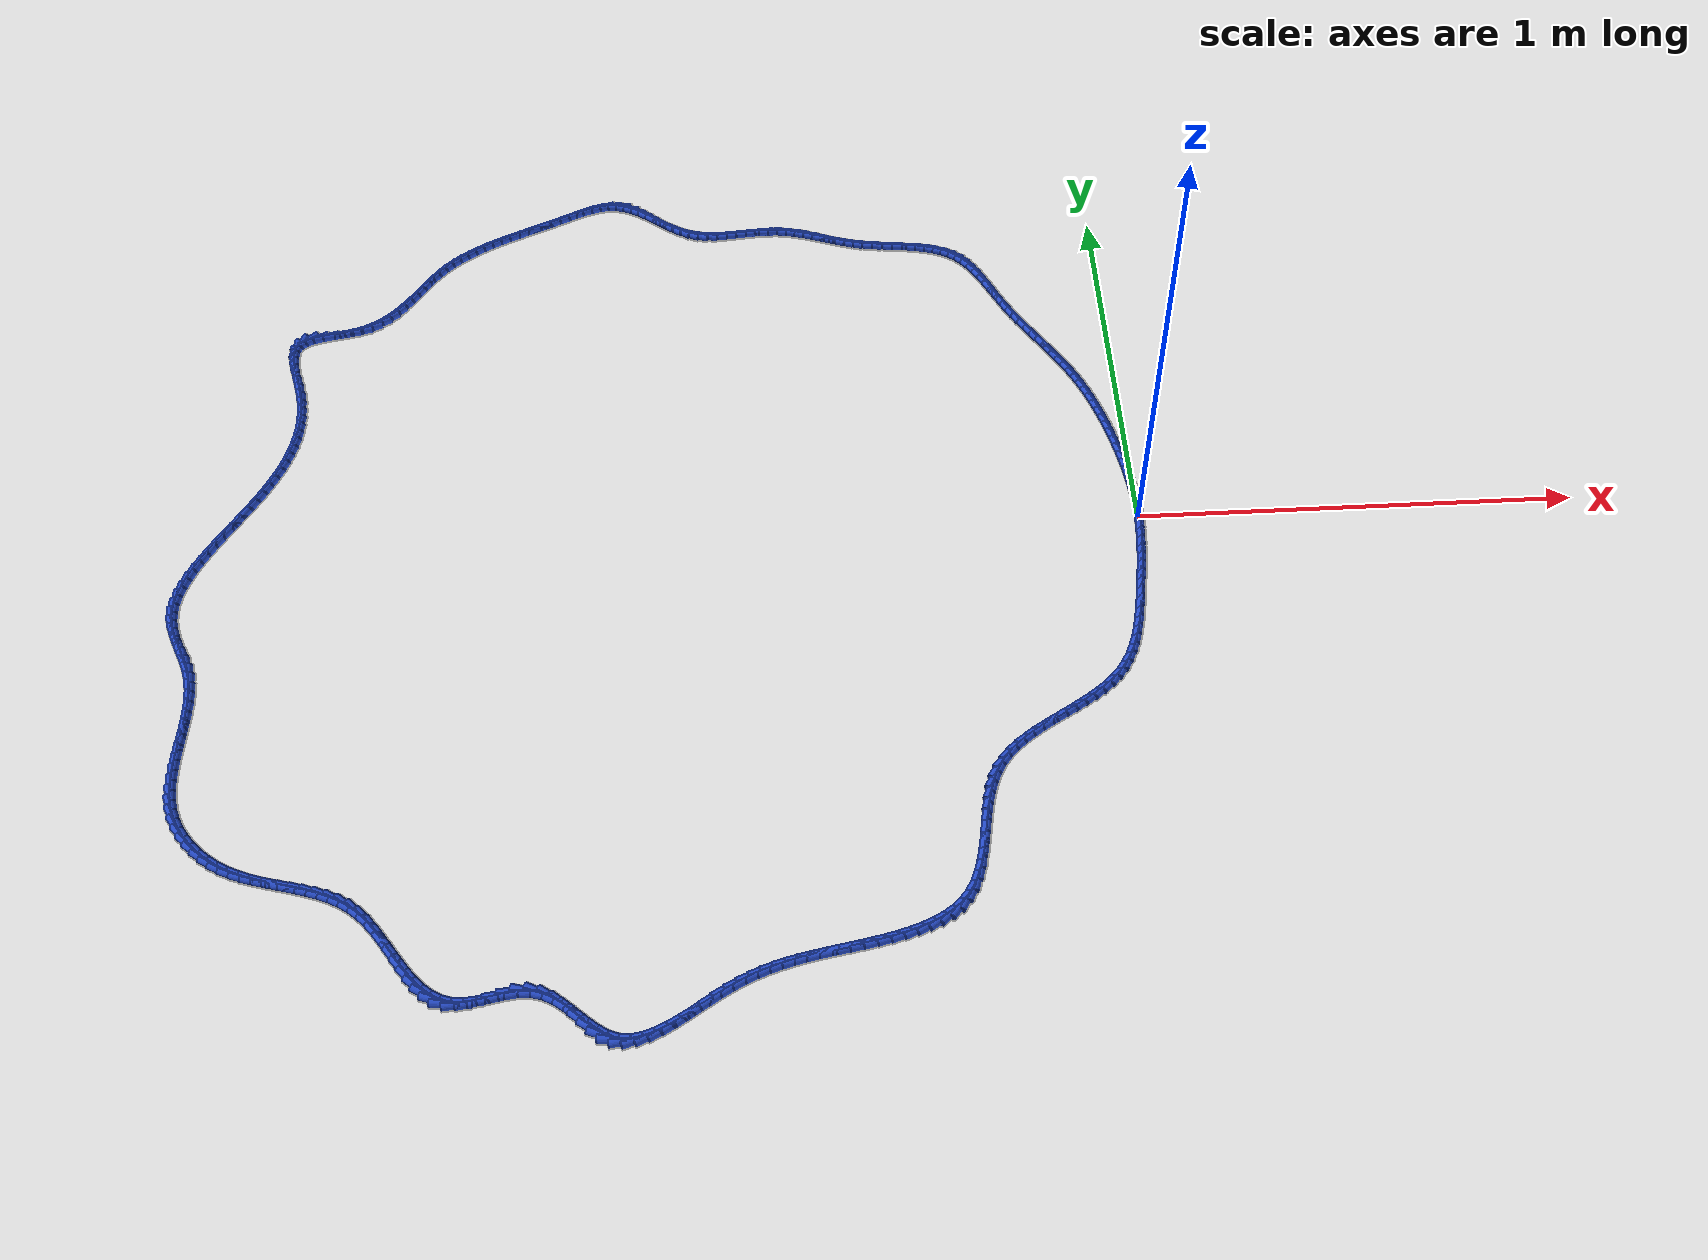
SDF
<sdf version="1.6">
 <world name="default">
  <light name="sun" type="directional">
   <pose>0 0 10 0 -0 0</pose>
   <diffuse>0.8 0.8 0.8 1</diffuse>
   <specular>0.2 0.2 0.2 1</specular>
   <attenuation>
    <range>1000</range>
    <constant>0.9</constant>
    <linear>0.01</linear>
    <quadratic>0.001</quadratic>
   </attenuation>
   <direction>-0.5 0.1 -0.9</direction>
  </light>
  <model name="ground_plane">
   <static>1</static>
   <link name="link">
    <collision name="collision">
     <geometry><plane><normal>0 0 1</normal><size>100 100</size></plane></geometry>
     <surface><friction><ode><mu>100</mu><mu2>50</mu2></ode></friction></surface>
    </collision>
    <visual name="visual">
     <cast_shadows>0</cast_shadows>
     <geometry><plane><normal>0 0 1</normal><size>100 100</size></plane></geometry>
     <material>
      <script><uri>file://media/materials/scripts/gazebo.material</uri><name>Gazebo/WhiteGlow</name></script>
     </material>
    </visual>
   </link>
  </model>
  <gravity>0 0 -9.8</gravity>
  <magnetic_field>6e-06 2.3e-05 -4.2e-05</magnetic_field>
  <atmosphere type="adiabatic"/>
  <physics name="default_physics" default="0" type="ode">
   <max_step_size>0.001</max_step_size>
   <real_time_factor>1</real_time_factor>
   <real_time_update_rate>1000</real_time_update_rate>
  </physics>
  <scene><ambient>0.4 0.4 0.4 1</ambient><background>0.7 0.7 0.7 1</background><shadows>1</shadows></scene>
  <spherical_coordinates>
   <surface_model>EARTH_WGS84</surface_model>
   <latitude_deg>0</latitude_deg>
   <longitude_deg>0</longitude_deg>
   <elevation>0</elevation>
   <heading_deg>0</heading_deg>
  </spherical_coordinates>
  <model name="line">
   <link name="link_0">
    <pose>-4.336808689942018e-18 -1.3877787807814457e-17 0.01 0 1.57 -1.56425743358107</pose>
    <collision name="collision">
     <geometry><cylinder><radius>0.01</radius><length>0.08</length></cylinder></geometry>
    </collision>
    <visual name="visual">
     <material>
      <script><name>Gazebo/Blue</name><uri>file://media/materials/scripts/gazebo.material</uri></script>
     </material>
     <geometry><cylinder><radius>0.01</radius><length>0.08</length></cylinder></geometry>
    </visual>
   </link>
   <link name="link_1">
    <pose>-0.00015712953239979557 0.024029646575687506 0.01 0 1.57 -1.534762119984785</pose>
    <collision name="collision">
     <geometry><cylinder><radius>0.01</radius><length>0.08</length></cylinder></geometry>
    </collision>
    <visual name="visual">
     <material>
      <script><name>Gazebo/Blue</name><uri>file://media/materials/scripts/gazebo.material</uri></script>
     </material>
     <geometry><cylinder><radius>0.01</radius><length>0.08</length></cylinder></geometry>
    </visual>
   </link>
   <link name="link_2">
    <pose>-0.0010254811451260578 0.048117196043376824 0.01 0 1.57 -1.5070020505178476</pose>
    <collision name="collision">
     <geometry><cylinder><radius>0.01</radius><length>0.08</length></cylinder></geometry>
    </collision>
    <visual name="visual">
     <material>
      <script><name>Gazebo/Blue</name><uri>file://media/materials/scripts/gazebo.material</uri></script>
     </material>
     <geometry><cylinder><radius>0.01</radius><length>0.08</length></cylinder></geometry>
    </visual>
   </link>
   <link name="link_3">
    <pose>-0.002566957849017019 0.07224765264961866 0.01 0 1.57 -1.4809456970232773</pose>
    <collision name="collision">
     <geometry><cylinder><radius>0.01</radius><length>0.08</length></cylinder></geometry>
    </collision>
    <visual name="visual">
     <material>
      <script><name>Gazebo/Blue</name><uri>file://media/materials/scripts/gazebo.material</uri></script>
     </material>
     <geometry><cylinder><radius>0.01</radius><length>0.08</length></cylinder></geometry>
    </visual>
   </link>
   <link name="link_4">
    <pose>-0.004743462654910904 0.09640602064096374 0.01 0 1.57 -1.4565549815009184</pose>
    <collision name="collision">
     <geometry><cylinder><radius>0.01</radius><length>0.08</length></cylinder></geometry>
    </collision>
    <visual name="visual">
     <material>
      <script><name>Gazebo/Blue</name><uri>file://media/materials/scripts/gazebo.material</uri></script>
     </material>
     <geometry><cylinder><radius>0.01</radius><length>0.08</length></cylinder></geometry>
    </visual>
   </link>
   <link name="link_5">
    <pose>-0.007516898573645941 0.12057730426396276 0.01 0 1.57 -1.4337875323644709</pose>
    <collision name="collision">
     <geometry><cylinder><radius>0.01</radius><length>0.08</length></cylinder></geometry>
    </collision>
    <visual name="visual">
     <material>
      <script><name>Gazebo/Blue</name><uri>file://media/materials/scripts/gazebo.material</uri></script>
     </material>
     <geometry><cylinder><radius>0.01</radius><length>0.08</length></cylinder></geometry>
    </visual>
   </link>
   <link name="link_6">
    <pose>-0.010849168616060355 0.14474650776516648 0.01 0 1.57 -1.4125986293645059</pose>
    <collision name="collision">
     <geometry><cylinder><radius>0.01</radius><length>0.08</length></cylinder></geometry>
    </collision>
    <visual name="visual">
     <material>
      <script><name>Gazebo/Blue</name><uri>file://media/materials/scripts/gazebo.material</uri></script>
     </material>
     <geometry><cylinder><radius>0.01</radius><length>0.08</length></cylinder></geometry>
    </visual>
   </link>
   <link name="link_7">
    <pose>-0.014702175792992371 0.16889863539112565 0.01 0 1.57 -1.3929428521763785</pose>
    <collision name="collision">
     <geometry><cylinder><radius>0.01</radius><length>0.08</length></cylinder></geometry>
    </collision>
    <visual name="visual">
     <material>
      <script><name>Gazebo/Blue</name><uri>file://media/materials/scripts/gazebo.material</uri></script>
     </material>
     <geometry><cylinder><radius>0.01</radius><length>0.08</length></cylinder></geometry>
    </visual>
   </link>
   <link name="link_8">
    <pose>-0.019037823115280218 0.19301869138839095 0.01 0 1.57 -1.374775146268974</pose>
    <collision name="collision">
     <geometry><cylinder><radius>0.01</radius><length>0.08</length></cylinder></geometry>
    </collision>
    <visual name="visual">
     <material>
      <script><name>Gazebo/Blue</name><uri>file://media/materials/scripts/gazebo.material</uri></script>
     </material>
     <geometry><cylinder><radius>0.01</radius><length>0.08</length></cylinder></geometry>
    </visual>
   </link>
   <link name="link_9">
    <pose>-0.023818020900240332 0.2170916772969812 0.01 0 1.57 -1.3574642948151834</pose>
    <collision name="collision">
     <geometry><cylinder><radius>0.01</radius><length>0.08</length></cylinder></geometry>
    </collision>
    <visual name="visual">
     <material>
      <script><name>Gazebo/Blue</name><uri>file://media/materials/scripts/gazebo.material</uri></script>
     </material>
     <geometry><cylinder><radius>0.01</radius><length>0.08</length></cylinder></geometry>
    </visual>
   </link>
   <link name="link_10">
    <pose>-0.02901836761405199 0.24109752416871083 0.01 0 1.57 -1.3391526477794322</pose>
    <collision name="collision">
     <geometry><cylinder><radius>0.01</radius><length>0.08</length></cylinder></geometry>
    </collision>
    <visual name="visual">
     <material>
      <script><name>Gazebo/Blue</name><uri>file://media/materials/scripts/gazebo.material</uri></script>
     </material>
     <geometry><cylinder><radius>0.01</radius><length>0.08</length></cylinder></geometry>
    </visual>
   </link>
   <link name="link_11">
    <pose>-0.03465656522533817 0.26500056669429106 0.01 0 1.57 -1.3194341095053292</pose>
    <collision name="collision">
     <geometry><cylinder><radius>0.01</radius><length>0.08</length></cylinder></geometry>
    </collision>
    <visual name="visual">
     <material>
      <script><name>Gazebo/Blue</name><uri>file://media/materials/scripts/gazebo.material</uri></script>
     </material>
     <geometry><cylinder><radius>0.01</radius><length>0.08</length></cylinder></geometry>
    </visual>
   </link>
   <link name="link_12">
    <pose>-0.04075838458038178 0.28876215061761396 0.01 0 1.57 -1.2982438296133518</pose>
    <collision name="collision">
     <geometry><cylinder><radius>0.01</radius><length>0.08</length></cylinder></geometry>
    </collision>
    <visual name="visual">
     <material>
      <script><name>Gazebo/Blue</name><uri>file://media/materials/scripts/gazebo.material</uri></script>
     </material>
     <geometry><cylinder><radius>0.01</radius><length>0.08</length></cylinder></geometry>
    </visual>
   </link>
   <link name="link_13">
    <pose>-0.04734959652546573 0.312343621682572 0.01 0 1.57 -1.2755126961789984</pose>
    <collision name="collision">
     <geometry><cylinder><radius>0.01</radius><length>0.08</length></cylinder></geometry>
    </collision>
    <visual name="visual">
     <material>
      <script><name>Gazebo/Blue</name><uri>file://media/materials/scripts/gazebo.material</uri></script>
     </material>
     <geometry><cylinder><radius>0.01</radius><length>0.08</length></cylinder></geometry>
    </visual>
   </link>
   <link name="link_14">
    <pose>-0.05445597190687294 0.33570632563305736 0.01 0 1.57 -1.251168259937428</pose>
    <collision name="collision">
     <geometry><cylinder><radius>0.01</radius><length>0.08</length></cylinder></geometry>
    </collision>
    <visual name="visual">
     <material>
      <script><name>Gazebo/Blue</name><uri>file://media/materials/scripts/gazebo.material</uri></script>
     </material>
     <geometry><cylinder><radius>0.01</radius><length>0.08</length></cylinder></geometry>
    </visual>
   </link>
   <link name="link_15">
    <pose>-0.062103281570886355 0.35881160821296265 0.01 0 1.57 -1.2251359467372962</pose>
    <collision name="collision">
     <geometry><cylinder><radius>0.01</radius><length>0.08</length></cylinder></geometry>
    </collision>
    <visual name="visual">
     <material>
      <script><name>Gazebo/Blue</name><uri>file://media/materials/scripts/gazebo.material</uri></script>
     </material>
     <geometry><cylinder><radius>0.01</radius><length>0.08</length></cylinder></geometry>
    </visual>
   </link>
   <link name="link_16">
    <pose>-0.07031729636378886 0.3816208151661799 0.01 0 1.57 -1.19734062881139</pose>
    <collision name="collision">
     <geometry><cylinder><radius>0.01</radius><length>0.08</length></cylinder></geometry>
    </collision>
    <visual name="visual">
     <material>
      <script><name>Gazebo/Blue</name><uri>file://media/materials/scripts/gazebo.material</uri></script>
     </material>
     <geometry><cylinder><radius>0.01</radius><length>0.08</length></cylinder></geometry>
    </visual>
   </link>
   <link name="link_17">
    <pose>-0.07912378713186341 0.40409529223660157 0.01 0 1.57 -1.167708628104993</pose>
    <collision name="collision">
     <geometry><cylinder><radius>0.01</radius><length>0.08</length></cylinder></geometry>
    </collision>
    <visual name="visual">
     <material>
      <script><name>Gazebo/Blue</name><uri>file://media/materials/scripts/gazebo.material</uri></script>
     </material>
     <geometry><cylinder><radius>0.01</radius><length>0.08</length></cylinder></geometry>
    </visual>
   </link>
   <link name="link_18">
    <pose>-0.08854852472139291 0.4261963851681201 0.01 0 1.57 -1.136170246248309</pose>
    <collision name="collision">
     <geometry><cylinder><radius>0.01</radius><length>0.08</length></cylinder></geometry>
    </collision>
    <visual name="visual">
     <material>
      <script><name>Gazebo/Blue</name><uri>file://media/materials/scripts/gazebo.material</uri></script>
     </material>
     <geometry><cylinder><radius>0.01</radius><length>0.08</length></cylinder></geometry>
    </visual>
   </link>
   <link name="link_19">
    <pose>-0.09861727955466063 0.4478854401632751 0.01 0 1.57 -1.1039069110874744</pose>
    <collision name="collision">
     <geometry><cylinder><radius>0.01</radius><length>0.08</length></cylinder></geometry>
    </collision>
    <visual name="visual">
     <material>
      <script><name>Gazebo/Blue</name><uri>file://media/materials/scripts/gazebo.material</uri></script>
     </material>
     <geometry><cylinder><radius>0.01</radius><length>0.08</length></cylinder></geometry>
    </visual>
   </link>
   <link name="link_20">
    <pose>-0.1093343643420875 0.46914701458705005 0.01 0 1.57 -1.0755684794429023</pose>
    <collision name="collision">
     <geometry><cylinder><radius>0.01</radius><length>0.08</length></cylinder></geometry>
    </collision>
    <visual name="visual">
     <material>
      <script><name>Gazebo/Blue</name><uri>file://media/materials/scripts/gazebo.material</uri></script>
     </material>
     <geometry><cylinder><radius>0.01</radius><length>0.08</length></cylinder></geometry>
    </visual>
   </link>
   <link name="link_21">
    <pose>-0.12062511963380591 0.4900510912986632 0.01 0 1.57 -1.0524000151151458</pose>
    <collision name="collision">
     <geometry><cylinder><radius>0.01</radius><length>0.08</length></cylinder></geometry>
    </collision>
    <visual name="visual">
     <material>
      <script><name>Gazebo/Blue</name><uri>file://media/materials/scripts/gazebo.material</uri></script>
     </material>
     <geometry><cylinder><radius>0.01</radius><length>0.08</length></cylinder></geometry>
    </visual>
   </link>
   <link name="link_22">
    <pose>-0.13239672260601829 0.5106873007798525 0.01 0 1.57 -1.0345260010369837</pose>
    <collision name="collision">
     <geometry><cylinder><radius>0.01</radius><length>0.08</length></cylinder></geometry>
    </collision>
    <visual name="visual">
     <material>
      <script><name>Gazebo/Blue</name><uri>file://media/materials/scripts/gazebo.material</uri></script>
     </material>
     <geometry><cylinder><radius>0.01</radius><length>0.08</length></cylinder></geometry>
    </visual>
   </link>
   <link name="link_23">
    <pose>-0.14455635043492715 0.5311452735123564 0.01 0 1.57 -1.0220009083321053</pose>
    <collision name="collision">
     <geometry><cylinder><radius>0.01</radius><length>0.08</length></cylinder></geometry>
    </collision>
    <visual name="visual">
     <material>
      <script><name>Gazebo/Blue</name><uri>file://media/materials/scripts/gazebo.material</uri></script>
     </material>
     <geometry><cylinder><radius>0.01</radius><length>0.08</length></cylinder></geometry>
    </visual>
   </link>
   <link name="link_24">
    <pose>-0.157011180296735 0.551514639977913 0.01 0 1.57 -1.0148236706591967</pose>
    <collision name="collision">
     <geometry><cylinder><radius>0.01</radius><length>0.08</length></cylinder></geometry>
    </collision>
    <visual name="visual">
     <material>
      <script><name>Gazebo/Blue</name><uri>file://media/materials/scripts/gazebo.material</uri></script>
     </material>
     <geometry><cylinder><radius>0.01</radius><length>0.08</length></cylinder></geometry>
    </visual>
   </link>
   <link name="link_25">
    <pose>-0.16966838936764422 0.57188503065826 0.01 0 1.57 -1.012949040087298</pose>
    <collision name="collision">
     <geometry><cylinder><radius>0.01</radius><length>0.08</length></cylinder></geometry>
    </collision>
    <visual name="visual">
     <material>
      <script><name>Gazebo/Blue</name><uri>file://media/materials/scripts/gazebo.material</uri></script>
     </material>
     <geometry><cylinder><radius>0.01</radius><length>0.08</length></cylinder></geometry>
    </visual>
   </link>
   <link name="link_26">
    <pose>-0.18243515482385728 0.592346076035136 0.01 0 1.57 -1.0162950817574345</pose>
    <collision name="collision">
     <geometry><cylinder><radius>0.01</radius><length>0.08</length></cylinder></geometry>
    </collision>
    <visual name="visual">
     <material>
      <script><name>Gazebo/Blue</name><uri>file://media/materials/scripts/gazebo.material</uri></script>
     </material>
     <geometry><cylinder><radius>0.01</radius><length>0.08</length></cylinder></geometry>
    </visual>
   </link>
   <link name="link_27">
    <pose>-0.1952186538415767 0.6129874065902788 0.01 0 1.57 -1.0247466729481558</pose>
    <collision name="collision">
     <geometry><cylinder><radius>0.01</radius><length>0.08</length></cylinder></geometry>
    </collision>
    <visual name="visual">
     <material>
      <script><name>Gazebo/Blue</name><uri>file://media/materials/scripts/gazebo.material</uri></script>
     </material>
     <geometry><cylinder><radius>0.01</radius><length>0.08</length></cylinder></geometry>
    </visual>
   </link>
   <link name="link_28">
    <pose>-0.20792606359700502 0.6338986528054272 0.01 0 1.57 -1.0381553246730917</pose>
    <collision name="collision">
     <geometry><cylinder><radius>0.01</radius><length>0.08</length></cylinder></geometry>
    </collision>
    <visual name="visual">
     <material>
      <script><name>Gazebo/Blue</name><uri>file://media/materials/scripts/gazebo.material</uri></script>
     </material>
     <geometry><cylinder><radius>0.01</radius><length>0.08</length></cylinder></geometry>
    </visual>
   </link>
   <link name="link_29">
    <pose>-0.22046456126634462 0.6551694451623188 0.01 0 1.57 -1.056335992029727</pose>
    <collision name="collision">
     <geometry><cylinder><radius>0.01</radius><length>0.08</length></cylinder></geometry>
    </collision>
    <visual name="visual">
     <material>
      <script><name>Gazebo/Blue</name><uri>file://media/materials/scripts/gazebo.material</uri></script>
     </material>
     <geometry><cylinder><radius>0.01</radius><length>0.08</length></cylinder></geometry>
    </visual>
   </link>
   <link name="link_30">
    <pose>-0.23274132402579786 0.6768894141426913 0.01 0 1.57 -1.0790618324481958</pose>
    <collision name="collision">
     <geometry><cylinder><radius>0.01</radius><length>0.08</length></cylinder></geometry>
    </collision>
    <visual name="visual">
     <material>
      <script><name>Gazebo/Blue</name><uri>file://media/materials/scripts/gazebo.material</uri></script>
     </material>
     <geometry><cylinder><radius>0.01</radius><length>0.08</length></cylinder></geometry>
    </visual>
   </link>
   <link name="link_31">
    <pose>-0.24466352905156738 0.6991481902282837 0.01 0 1.57 -1.1055376811638797</pose>
    <collision name="collision">
     <geometry><cylinder><radius>0.01</radius><length>0.08</length></cylinder></geometry>
    </collision>
    <visual name="visual">
     <material>
      <script><name>Gazebo/Blue</name><uri>file://media/materials/scripts/gazebo.material</uri></script>
     </material>
     <geometry><cylinder><radius>0.01</radius><length>0.08</length></cylinder></geometry>
    </visual>
   </link>
   <link name="link_32">
    <pose>-0.25614729190583174 0.7220235091410367 0.01 0 1.57 -1.1254862418766172</pose>
    <collision name="collision">
     <geometry><cylinder><radius>0.01</radius><length>0.08</length></cylinder></geometry>
    </collision>
    <visual name="visual">
     <material>
      <script><name>Gazebo/Blue</name><uri>file://media/materials/scripts/gazebo.material</uri></script>
     </material>
     <geometry><cylinder><radius>0.01</radius><length>0.08</length></cylinder></geometry>
    </visual>
   </link>
   <link name="link_33">
    <pose>-0.2672848295646846 0.745358759593939 0.01 0 1.57 -1.1302014294361307</pose>
    <collision name="collision">
     <geometry><cylinder><radius>0.01</radius><length>0.08</length></cylinder></geometry>
    </collision>
    <visual name="visual">
     <material>
      <script><name>Gazebo/Blue</name><uri>file://media/materials/scripts/gazebo.material</uri></script>
     </material>
     <geometry><cylinder><radius>0.01</radius><length>0.08</length></cylinder></geometry>
    </visual>
   </link>
   <link name="link_34">
    <pose>-0.27832948961504517 0.7687829056916885 0.01 0 1.57 -1.1195346656095904</pose>
    <collision name="collision">
     <geometry><cylinder><radius>0.01</radius><length>0.08</length></cylinder></geometry>
    </collision>
    <visual name="visual">
     <material>
      <script><name>Gazebo/Blue</name><uri>file://media/materials/scripts/gazebo.material</uri></script>
     </material>
     <geometry><cylinder><radius>0.01</radius><length>0.08</length></cylinder></geometry>
    </visual>
   </link>
   <link name="link_35">
    <pose>-0.2895405564584305 0.791917011121192 0.01 0 1.57 -1.0928588952908276</pose>
    <collision name="collision">
     <geometry><cylinder><radius>0.01</radius><length>0.08</length></cylinder></geometry>
    </collision>
    <visual name="visual">
     <material>
      <script><name>Gazebo/Blue</name><uri>file://media/materials/scripts/gazebo.material</uri></script>
     </material>
     <geometry><cylinder><radius>0.01</radius><length>0.08</length></cylinder></geometry>
    </visual>
   </link>
   <link name="link_36">
    <pose>-0.30117731449635726 0.8143821395693573 0.01 0 1.57 -1.0487222438221038</pose>
    <collision name="collision">
     <geometry><cylinder><radius>0.01</radius><length>0.08</length></cylinder></geometry>
    </collision>
    <visual name="visual">
     <material>
      <script><name>Gazebo/Blue</name><uri>file://media/materials/scripts/gazebo.material</uri></script>
     </material>
     <geometry><cylinder><radius>0.01</radius><length>0.08</length></cylinder></geometry>
    </visual>
   </link>
   <link name="link_37">
    <pose>-0.31349904813034224 0.8357993547230914 0.01 0 1.57 -0.9849063638331867</pose>
    <collision name="collision">
     <geometry><cylinder><radius>0.01</radius><length>0.08</length></cylinder></geometry>
    </collision>
    <visual name="visual">
     <material>
      <script><name>Gazebo/Blue</name><uri>file://media/materials/scripts/gazebo.material</uri></script>
     </material>
     <geometry><cylinder><radius>0.01</radius><length>0.08</length></cylinder></geometry>
    </visual>
   </link>
   <link name="link_38">
    <pose>-0.326765041761902 0.8557897202693008 0.01 0 1.57 -0.8986805505302923</pose>
    <collision name="collision">
     <geometry><cylinder><radius>0.01</radius><length>0.08</length></cylinder></geometry>
    </collision>
    <visual name="visual">
     <material>
      <script><name>Gazebo/Blue</name><uri>file://media/materials/scripts/gazebo.material</uri></script>
     </material>
     <geometry><cylinder><radius>0.01</radius><length>0.08</length></cylinder></geometry>
    </visual>
   </link>
   <link name="link_39">
    <pose>-0.3412345797925537 0.8739742998948934 0.01 0 1.57 -0.7875117167677026</pose>
    <collision name="collision">
     <geometry><cylinder><radius>0.01</radius><length>0.08</length></cylinder></geometry>
    </collision>
    <visual name="visual">
     <material>
      <script><name>Gazebo/Blue</name><uri>file://media/materials/scripts/gazebo.material</uri></script>
     </material>
     <geometry><cylinder><radius>0.01</radius><length>0.08</length></cylinder></geometry>
    </visual>
   </link>
   <link name="link_40">
    <pose>-0.35716694662381376 0.8899741572867759 0.01 0 1.57 -0.6506448861718576</pose>
    <collision name="collision">
     <geometry><cylinder><radius>0.01</radius><length>0.08</length></cylinder></geometry>
    </collision>
    <visual name="visual">
     <material>
      <script><name>Gazebo/Blue</name><uri>file://media/materials/scripts/gazebo.material</uri></script>
     </material>
     <geometry><cylinder><radius>0.01</radius><length>0.08</length></cylinder></geometry>
    </visual>
   </link>
   <link name="link_41">
    <pose>-0.3748202287327567 0.9034122323183431 0.01 0 1.57 -0.5041839313609928</pose>
    <collision name="collision">
     <geometry><cylinder><radius>0.01</radius><length>0.08</length></cylinder></geometry>
    </collision>
    <visual name="visual">
     <material>
      <script><name>Gazebo/Blue</name><uri>file://media/materials/scripts/gazebo.material</uri></script>
     </material>
     <geometry><cylinder><radius>0.01</radius><length>0.08</length></cylinder></geometry>
    </visual>
   </link>
   <link name="link_42">
    <pose>-0.39429536380937463 0.9141575909294289 0.01 0 1.57 -0.37952432522848406</pose>
    <collision name="collision">
     <geometry><cylinder><radius>0.01</radius><length>0.08</length></cylinder></geometry>
    </collision>
    <visual name="visual">
     <material>
      <script><name>Gazebo/Blue</name><uri>file://media/materials/scripts/gazebo.material</uri></script>
     </material>
     <geometry><cylinder><radius>0.01</radius><length>0.08</length></cylinder></geometry>
    </visual>
   </link>
   <link name="link_43">
    <pose>-0.41538129094751364 0.9225679505386968 0.01 0 1.57 -0.2814588411012128</pose>
    <collision name="collision">
     <geometry><cylinder><radius>0.01</radius><length>0.08</length></cylinder></geometry>
    </collision>
    <visual name="visual">
     <material>
      <script><name>Gazebo/Blue</name><uri>file://media/materials/scripts/gazebo.material</uri></script>
     </material>
     <geometry><cylinder><radius>0.01</radius><length>0.08</length></cylinder></geometry>
    </visual>
   </link>
   <link name="link_44">
    <pose>-0.4378301360946045 0.9290586852294832 0.01 0 1.57 -0.20853894303594395</pose>
    <collision name="collision">
     <geometry><cylinder><radius>0.01</radius><length>0.08</length></cylinder></geometry>
    </collision>
    <visual name="visual">
     <material>
      <script><name>Gazebo/Blue</name><uri>file://media/materials/scripts/gazebo.material</uri></script>
     </material>
     <geometry><cylinder><radius>0.01</radius><length>0.08</length></cylinder></geometry>
    </visual>
   </link>
   <link name="link_45">
    <pose>-0.4613940251980771 0.9340451690851242 0.01 0 1.57 -0.1582017605530551</pose>
    <collision name="collision">
     <geometry><cylinder><radius>0.01</radius><length>0.08</length></cylinder></geometry>
    </collision>
    <visual name="visual">
     <material>
      <script><name>Gazebo/Blue</name><uri>file://media/materials/scripts/gazebo.material</uri></script>
     </material>
     <geometry><cylinder><radius>0.01</radius><length>0.08</length></cylinder></geometry>
    </visual>
   </link>
   <link name="link_46">
    <pose>-0.4858250842053616 0.9379427761889566 0.01 0 1.57 -0.12800125727517256</pose>
    <collision name="collision">
     <geometry><cylinder><radius>0.01</radius><length>0.08</length></cylinder></geometry>
    </collision>
    <visual name="visual">
     <material>
      <script><name>Gazebo/Blue</name><uri>file://media/materials/scripts/gazebo.material</uri></script>
     </material>
     <geometry><cylinder><radius>0.01</radius><length>0.08</length></cylinder></geometry>
    </visual>
   </link>
   <link name="link_47">
    <pose>-0.5108754390638885 0.9411668806243169 0.01 0 1.57 -0.11614558169399034</pose>
    <collision name="collision">
     <geometry><cylinder><radius>0.01</radius><length>0.08</length></cylinder></geometry>
    </collision>
    <visual name="visual">
     <material>
      <script><name>Gazebo/Blue</name><uri>file://media/materials/scripts/gazebo.material</uri></script>
     </material>
     <geometry><cylinder><radius>0.01</radius><length>0.08</length></cylinder></geometry>
    </visual>
   </link>
   <link name="link_48">
    <pose>-0.5362972157210881 0.9441328564745414 0.01 0 1.57 -0.12165817281398095</pose>
    <collision name="collision">
     <geometry><cylinder><radius>0.01</radius><length>0.08</length></cylinder></geometry>
    </collision>
    <visual name="visual">
     <material>
      <script><name>Gazebo/Blue</name><uri>file://media/materials/scripts/gazebo.material</uri></script>
     </material>
     <geometry><cylinder><radius>0.01</radius><length>0.08</length></cylinder></geometry>
    </visual>
   </link>
   <link name="link_49">
    <pose>-0.5618425401243904 0.9472560778229667 0.01 0 1.57 -0.14437382453169778</pose>
    <collision name="collision">
     <geometry><cylinder><radius>0.01</radius><length>0.08</length></cylinder></geometry>
    </collision>
    <visual name="visual">
     <material>
      <script><name>Gazebo/Blue</name><uri>file://media/materials/scripts/gazebo.material</uri></script>
     </material>
     <geometry><cylinder><radius>0.01</radius><length>0.08</length></cylinder></geometry>
    </visual>
   </link>
   <link name="link_50">
    <pose>-0.5872635382212257 0.9509519187529292 0.01 0 1.57 -0.18485367870743535</pose>
    <collision name="collision">
     <geometry><cylinder><radius>0.01</radius><length>0.08</length></cylinder></geometry>
    </collision>
    <visual name="visual">
     <material>
      <script><name>Gazebo/Blue</name><uri>file://media/materials/scripts/gazebo.material</uri></script>
     </material>
     <geometry><cylinder><radius>0.01</radius><length>0.08</length></cylinder></geometry>
    </visual>
   </link>
   <link name="link_51">
    <pose>-0.6123123359590241 0.9556357533477657 0.01 0 1.57 -0.24248156528016612</pose>
    <collision name="collision">
     <geometry><cylinder><radius>0.01</radius><length>0.08</length></cylinder></geometry>
    </collision>
    <visual name="visual">
     <material>
      <script><name>Gazebo/Blue</name><uri>file://media/materials/scripts/gazebo.material</uri></script>
     </material>
     <geometry><cylinder><radius>0.01</radius><length>0.08</length></cylinder></geometry>
    </visual>
   </link>
   <link name="link_52">
    <pose>-0.6367590903299265 0.9616826209630372 0.01 0 1.57 -0.29671909833897947</pose>
    <collision name="collision">
     <geometry><cylinder><radius>0.01</radius><length>0.08</length></cylinder></geometry>
    </collision>
    <visual name="visual">
     <material>
      <script><name>Gazebo/Blue</name><uri>file://media/materials/scripts/gazebo.material</uri></script>
     </material>
     <geometry><cylinder><radius>0.01</radius><length>0.08</length></cylinder></geometry>
    </visual>
   </link>
   <link name="link_53">
    <pose>-0.6605960884370088 0.9689706647567197 0.01 0 1.57 -0.3326209452795181</pose>
    <collision name="collision">
     <geometry><cylinder><radius>0.01</radius><length>0.08</length></cylinder></geometry>
    </collision>
    <visual name="visual">
     <material>
      <script><name>Gazebo/Blue</name><uri>file://media/materials/scripts/gazebo.material</uri></script>
     </material>
     <geometry><cylinder><radius>0.01</radius><length>0.08</length></cylinder></geometry>
    </visual>
   </link>
   <link name="link_54">
    <pose>-0.6839651048086288 0.977043630479352 0.01 0 1.57 -0.3493529996150852</pose>
    <collision name="collision">
     <geometry><cylinder><radius>0.01</radius><length>0.08</length></cylinder></geometry>
    </collision>
    <visual name="visual">
     <material>
      <script><name>Gazebo/Blue</name><uri>file://media/materials/scripts/gazebo.material</uri></script>
     </material>
     <geometry><cylinder><radius>0.01</radius><length>0.08</length></cylinder></geometry>
    </visual>
   </link>
   <link name="link_55">
    <pose>-0.7070106982817136 0.9854390354942713 0.01 0 1.57 -0.34645884245418296</pose>
    <collision name="collision">
     <geometry><cylinder><radius>0.01</radius><length>0.08</length></cylinder></geometry>
    </collision>
    <visual name="visual">
     <material>
      <script><name>Gazebo/Blue</name><uri>file://media/materials/scripts/gazebo.material</uri></script>
     </material>
     <geometry><cylinder><radius>0.01</radius><length>0.08</length></cylinder></geometry>
    </visual>
   </link>
   <link name="link_56">
    <pose>-0.7298774276931896 0.993694397164814 0.01 0 1.57 -0.3234062679523985</pose>
    <collision name="collision">
     <geometry><cylinder><radius>0.01</radius><length>0.08</length></cylinder></geometry>
    </collision>
    <visual name="visual">
     <material>
      <script><name>Gazebo/Blue</name><uri>file://media/materials/scripts/gazebo.material</uri></script>
     </material>
     <geometry><cylinder><radius>0.01</radius><length>0.08</length></cylinder></geometry>
    </visual>
   </link>
   <link name="link_57">
    <pose>-0.7527098518799834 1.0013472328543171 0.01 0 1.57 -0.27961995573969894</pose>
    <collision name="collision">
     <geometry><cylinder><radius>0.01</radius><length>0.08</length></cylinder></geometry>
    </collision>
    <visual name="visual">
     <material>
      <script><name>Gazebo/Blue</name><uri>file://media/materials/scripts/gazebo.material</uri></script>
     </material>
     <geometry><cylinder><radius>0.01</radius><length>0.08</length></cylinder></geometry>
    </visual>
   </link>
   <link name="link_58">
    <pose>-0.7756525296790209 1.0079350599261168 0.01 0 1.57 -0.21477693447434978</pose>
    <collision name="collision">
     <geometry><cylinder><radius>0.01</radius><length>0.08</length></cylinder></geometry>
    </collision>
    <visual name="visual">
     <material>
      <script><name>Gazebo/Blue</name><uri>file://media/materials/scripts/gazebo.material</uri></script>
     </material>
     <geometry><cylinder><radius>0.01</radius><length>0.08</length></cylinder></geometry>
    </visual>
   </link>
   <link name="link_59">
    <pose>-0.7988500199272289 1.0129953957435496 0.01 0 1.57 -0.12939512095294445</pose>
    <collision name="collision">
     <geometry><cylinder><radius>0.01</radius><length>0.08</length></cylinder></geometry>
    </collision>
    <visual name="visual">
     <material>
      <script><name>Gazebo/Blue</name><uri>file://media/materials/scripts/gazebo.material</uri></script>
     </material>
     <geometry><cylinder><radius>0.01</radius><length>0.08</length></cylinder></geometry>
    </visual>
   </link>
   <link name="link_60">
    <pose>-0.8224468537431318 1.016065866464279 0.01 0 1.57 -0.03542578522712086</pose>
    <collision name="collision">
     <geometry><cylinder><radius>0.01</radius><length>0.08</length></cylinder></geometry>
    </collision>
    <visual name="visual">
     <material>
      <script><name>Gazebo/Blue</name><uri>file://media/materials/scripts/gazebo.material</uri></script>
     </material>
     <geometry><cylinder><radius>0.01</radius><length>0.08</length></cylinder></geometry>
    </visual>
   </link>
   <link name="link_61">
    <pose>-0.8465276369474751 1.01691930416558 0.01 0 1.57 0.03504976159609683</pose>
    <collision name="collision">
     <geometry><cylinder><radius>0.01</radius><length>0.08</length></cylinder></geometry>
    </collision>
    <visual name="visual">
     <material>
      <script><name>Gazebo/Blue</name><uri>file://media/materials/scripts/gazebo.material</uri></script>
     </material>
     <geometry><cylinder><radius>0.01</radius><length>0.08</length></cylinder></geometry>
    </visual>
   </link>
   <link name="link_62">
    <pose>-0.8709902220071917 1.0160615451141743 0.01 0 1.57 0.07758760818371419</pose>
    <collision name="collision">
     <geometry><cylinder><radius>0.01</radius><length>0.08</length></cylinder></geometry>
    </collision>
    <visual name="visual">
     <material>
      <script><name>Gazebo/Blue</name><uri>file://media/materials/scripts/gazebo.material</uri></script>
     </material>
     <geometry><cylinder><radius>0.01</radius><length>0.08</length></cylinder></geometry>
    </visual>
   </link>
   <link name="link_63">
    <pose>-0.8956961842332929 1.0141408128845788 0.01 0 1.57 0.09385467288671161</pose>
    <collision name="collision">
     <geometry><cylinder><radius>0.01</radius><length>0.08</length></cylinder></geometry>
    </collision>
    <visual name="visual">
     <material>
      <script><name>Gazebo/Blue</name><uri>file://media/materials/scripts/gazebo.material</uri></script>
     </material>
     <geometry><cylinder><radius>0.01</radius><length>0.08</length></cylinder></geometry>
    </visual>
   </link>
   <link name="link_64">
    <pose>-0.9205070989367906 1.0118053310513109 0.01 0 1.57 0.08463289792137456</pose>
    <collision name="collision">
     <geometry><cylinder><radius>0.01</radius><length>0.08</length></cylinder></geometry>
    </collision>
    <visual name="visual">
     <material>
      <script><name>Gazebo/Blue</name><uri>file://media/materials/scripts/gazebo.material</uri></script>
     </material>
     <geometry><cylinder><radius>0.01</radius><length>0.08</length></cylinder></geometry>
    </visual>
   </link>
   <link name="link_65">
    <pose>-0.9452845414286959 1.0097033231888868 0.01 0 1.57 0.04955432796736535</pose>
    <collision name="collision">
     <geometry><cylinder><radius>0.01</radius><length>0.08</length></cylinder></geometry>
    </collision>
    <visual name="visual">
     <material>
      <script><name>Gazebo/Blue</name><uri>file://media/materials/scripts/gazebo.material</uri></script>
     </material>
     <geometry><cylinder><radius>0.01</radius><length>0.08</length></cylinder></geometry>
    </visual>
   </link>
   <link name="link_66">
    <pose>-0.96989008702002 1.0084830128718227 0.01 0 1.57 -0.012743000187645999</pose>
    <collision name="collision">
     <geometry><cylinder><radius>0.01</radius><length>0.08</length></cylinder></geometry>
    </collision>
    <visual name="visual">
     <material>
      <script><name>Gazebo/Blue</name><uri>file://media/materials/scripts/gazebo.material</uri></script>
     </material>
     <geometry><cylinder><radius>0.01</radius><length>0.08</length></cylinder></geometry>
    </visual>
   </link>
   <link name="link_67">
    <pose>-0.994185311021775 1.0087926236746365 0.01 0 1.57 -0.10394779802994805</pose>
    <collision name="collision">
     <geometry><cylinder><radius>0.01</radius><length>0.08</length></cylinder></geometry>
    </collision>
    <visual name="visual">
     <material>
      <script><name>Gazebo/Blue</name><uri>file://media/materials/scripts/gazebo.material</uri></script>
     </material>
     <geometry><cylinder><radius>0.01</radius><length>0.08</length></cylinder></geometry>
    </visual>
   </link>
   <link name="link_68">
    <pose>-1.0180317887449721 1.0112803791718439 0.01 0 1.57 -0.22461763200873708</pose>
    <collision name="collision">
     <geometry><cylinder><radius>0.01</radius><length>0.08</length></cylinder></geometry>
    </collision>
    <visual name="visual">
     <material>
      <script><name>Gazebo/Blue</name><uri>file://media/materials/scripts/gazebo.material</uri></script>
     </material>
     <geometry><cylinder><radius>0.01</radius><length>0.08</length></cylinder></geometry>
    </visual>
   </link>
   <link name="link_69">
    <pose>-1.0412910955006227 1.0165945029379624 0.01 0 1.57 -0.3684386136101896</pose>
    <collision name="collision">
     <geometry><cylinder><radius>0.01</radius><length>0.08</length></cylinder></geometry>
    </collision>
    <visual name="visual">
     <material>
      <script><name>Gazebo/Blue</name><uri>file://media/materials/scripts/gazebo.material</uri></script>
     </material>
     <geometry><cylinder><radius>0.01</radius><length>0.08</length></cylinder></geometry>
    </visual>
   </link>
   <link name="link_70">
    <pose>-1.0638398889554026 1.0252998698394604 0.01 0 1.57 -0.49391397376150475</pose>
    <collision name="collision">
     <geometry><cylinder><radius>0.01</radius><length>0.08</length></cylinder></geometry>
    </collision>
    <visual name="visual">
     <material>
      <script><name>Gazebo/Blue</name><uri>file://media/materials/scripts/gazebo.material</uri></script>
     </material>
     <geometry><cylinder><radius>0.01</radius><length>0.08</length></cylinder></geometry>
    </visual>
   </link>
   <link name="link_71">
    <pose>-1.0857147026035259 1.037077842646319 0.01 0 1.57 -0.5807513590610146</pose>
    <collision name="collision">
     <geometry><cylinder><radius>0.01</radius><length>0.08</length></cylinder></geometry>
    </collision>
    <visual name="visual">
     <material>
      <script><name>Gazebo/Blue</name><uri>file://media/materials/scripts/gazebo.material</uri></script>
     </material>
     <geometry><cylinder><radius>0.01</radius><length>0.08</length></cylinder></geometry>
    </visual>
   </link>
   <link name="link_72">
    <pose>-1.1070483210717446 1.0510778773280445 0.01 0 1.57 -0.6333120152724254</pose>
    <collision name="collision">
     <geometry><cylinder><radius>0.01</radius><length>0.08</length></cylinder></geometry>
    </collision>
    <visual name="visual">
     <material>
      <script><name>Gazebo/Blue</name><uri>file://media/materials/scripts/gazebo.material</uri></script>
     </material>
     <geometry><cylinder><radius>0.01</radius><length>0.08</length></cylinder></geometry>
    </visual>
   </link>
   <link name="link_73">
    <pose>-1.1279748500396338 1.0664421293999844 0.01 0 1.57 -0.6551869053698643</pose>
    <collision name="collision">
     <geometry><cylinder><radius>0.01</radius><length>0.08</length></cylinder></geometry>
    </collision>
    <visual name="visual">
     <material>
      <script><name>Gazebo/Blue</name><uri>file://media/materials/scripts/gazebo.material</uri></script>
     </material>
     <geometry><cylinder><radius>0.01</radius><length>0.08</length></cylinder></geometry>
    </visual>
   </link>
   <link name="link_74">
    <pose>-1.1486283951867695 1.082312754377485 0.01 0 1.57 -0.6476421876659263</pose>
    <collision name="collision">
     <geometry><cylinder><radius>0.01</radius><length>0.08</length></cylinder></geometry>
    </collision>
    <visual name="visual">
     <material>
      <script><name>Gazebo/Blue</name><uri>file://media/materials/scripts/gazebo.material</uri></script>
     </material>
     <geometry><cylinder><radius>0.01</radius><length>0.08</length></cylinder></geometry>
    </visual>
   </link>
   <link name="link_75">
    <pose>-1.1691430621927281 1.0978319077758942 0.01 0 1.57 -0.6091834234467767</pose>
    <collision name="collision">
     <geometry><cylinder><radius>0.01</radius><length>0.08</length></cylinder></geometry>
    </collision>
    <visual name="visual">
     <material>
      <script><name>Gazebo/Blue</name><uri>file://media/materials/scripts/gazebo.material</uri></script>
     </material>
     <geometry><cylinder><radius>0.01</radius><length>0.08</length></cylinder></geometry>
    </visual>
   </link>
   <link name="link_76">
    <pose>-1.189652956737085 1.1121417451105584 0.01 0 1.57 -0.5353861067403141</pose>
    <collision name="collision">
     <geometry><cylinder><radius>0.01</radius><length>0.08</length></cylinder></geometry>
    </collision>
    <visual name="visual">
     <material>
      <script><name>Gazebo/Blue</name><uri>file://media/materials/scripts/gazebo.material</uri></script>
     </material>
     <geometry><cylinder><radius>0.01</radius><length>0.08</length></cylinder></geometry>
    </visual>
   </link>
   <link name="link_77">
    <pose>-1.2102921844994172 1.1243844218968255 0.01 0 1.57 -0.41932630337566856</pose>
    <collision name="collision">
     <geometry><cylinder><radius>0.01</radius><length>0.08</length></cylinder></geometry>
    </collision>
    <visual name="visual">
     <material>
      <script><name>Gazebo/Blue</name><uri>file://media/materials/scripts/gazebo.material</uri></script>
     </material>
     <geometry><cylinder><radius>0.01</radius><length>0.08</length></cylinder></geometry>
    </visual>
   </link>
   <link name="link_78">
    <pose>-1.2311948511592994 1.1337020936500417 0.01 0 1.57 -0.2542258953793268</pose>
    <collision name="collision">
     <geometry><cylinder><radius>0.01</radius><length>0.08</length></cylinder></geometry>
    </collision>
    <visual name="visual">
     <material>
      <script><name>Gazebo/Blue</name><uri>file://media/materials/scripts/gazebo.material</uri></script>
     </material>
     <geometry><cylinder><radius>0.01</radius><length>0.08</length></cylinder></geometry>
    </visual>
   </link>
   <link name="link_79">
    <pose>-1.2524950623963083 1.1392369158855542 0.01 0 1.57 -0.04357714665242913</pose>
    <collision name="collision">
     <geometry><cylinder><radius>0.01</radius><length>0.08</length></cylinder></geometry>
    </collision>
    <visual name="visual">
     <material>
      <script><name>Gazebo/Blue</name><uri>file://media/materials/scripts/gazebo.material</uri></script>
     </material>
     <geometry><cylinder><radius>0.01</radius><length>0.08</length></cylinder></geometry>
    </visual>
   </link>
   <link name="link_80">
    <pose>-1.2743191834197212 1.1401885512591738 0.01 0 1.57 0.15494856343534053</pose>
    <collision name="collision">
     <geometry><cylinder><radius>0.01</radius><length>0.08</length></cylinder></geometry>
    </collision>
    <visual name="visual">
     <material>
      <script><name>Gazebo/Blue</name><uri>file://media/materials/scripts/gazebo.material</uri></script>
     </material>
     <geometry><cylinder><radius>0.01</radius><length>0.08</length></cylinder></geometry>
    </visual>
   </link>
   <link name="link_81">
    <pose>-1.2966668989865384 1.1366978236588285 0.01 0 1.57 0.2992500020910055</pose>
    <collision name="collision">
     <geometry><cylinder><radius>0.01</radius><length>0.08</length></cylinder></geometry>
    </collision>
    <visual name="visual">
     <material>
      <script><name>Gazebo/Blue</name><uri>file://media/materials/scripts/gazebo.material</uri></script>
     </material>
     <geometry><cylinder><radius>0.01</radius><length>0.08</length></cylinder></geometry>
    </visual>
   </link>
   <link name="link_82">
    <pose>-1.3194345039125746 1.1296736834093672 0.01 0 1.57 0.39512939659951296</pose>
    <collision name="collision">
     <geometry><cylinder><radius>0.01</radius><length>0.08</length></cylinder></geometry>
    </collision>
    <visual name="visual">
     <material>
      <script><name>Gazebo/Blue</name><uri>file://media/materials/scripts/gazebo.material</uri></script>
     </material>
     <geometry><cylinder><radius>0.01</radius><length>0.08</length></cylinder></geometry>
    </visual>
   </link>
   <link name="link_83">
    <pose>-1.3425152709971997 1.1200475326399078 0.01 0 1.57 0.45166149255052174</pose>
    <collision name="collision">
     <geometry><cylinder><radius>0.01</radius><length>0.08</length></cylinder></geometry>
    </collision>
    <visual name="visual">
     <material>
      <script><name>Gazebo/Blue</name><uri>file://media/materials/scripts/gazebo.material</uri></script>
     </material>
     <geometry><cylinder><radius>0.01</radius><length>0.08</length></cylinder></geometry>
    </visual>
   </link>
   <link name="link_84">
    <pose>-1.365802473039785 1.1087507734795696 0.01 0 1.57 0.47529516162897273</pose>
    <collision name="collision">
     <geometry><cylinder><radius>0.01</radius><length>0.08</length></cylinder></geometry>
    </collision>
    <visual name="visual">
     <material>
      <script><name>Gazebo/Blue</name><uri>file://media/materials/scripts/gazebo.material</uri></script>
     </material>
     <geometry><cylinder><radius>0.01</radius><length>0.08</length></cylinder></geometry>
    </visual>
   </link>
   <link name="link_85">
    <pose>-1.3891893828397013 1.0967148080574727 0.01 0 1.57 0.4707790373488146</pose>
    <collision name="collision">
     <geometry><cylinder><radius>0.01</radius><length>0.08</length></cylinder></geometry>
    </collision>
    <visual name="visual">
     <material>
      <script><name>Gazebo/Blue</name><uri>file://media/materials/scripts/gazebo.material</uri></script>
     </material>
     <geometry><cylinder><radius>0.01</radius><length>0.08</length></cylinder></geometry>
    </visual>
   </link>
   <link name="link_86">
    <pose>-1.4125705870942782 1.084815029793274 0.01 0 1.57 0.459084178298226</pose>
    <collision name="collision">
     <geometry><cylinder><radius>0.01</radius><length>0.08</length></cylinder></geometry>
    </collision>
    <visual name="visual">
     <material>
      <script><name>Gazebo/Blue</name><uri>file://media/materials/scripts/gazebo.material</uri></script>
     </material>
     <geometry><cylinder><radius>0.01</radius><length>0.08</length></cylinder></geometry>
    </visual>
   </link>
   <link name="link_87">
    <pose>-1.4358552548566486 1.0733052169164998 0.01 0 1.57 0.45321910208213384</pose>
    <collision name="collision">
     <geometry><cylinder><radius>0.01</radius><length>0.08</length></cylinder></geometry>
    </collision>
    <visual name="visual">
     <material>
      <script><name>Gazebo/Blue</name><uri>file://media/materials/scripts/gazebo.material</uri></script>
     </material>
     <geometry><cylinder><radius>0.01</radius><length>0.08</length></cylinder></geometry>
    </visual>
   </link>
   <link name="link_88">
    <pose>-1.45896164478779 1.0620516767717623 0.01 0 1.57 0.45356805085304674</pose>
    <collision name="collision">
     <geometry><cylinder><radius>0.01</radius><length>0.08</length></cylinder></geometry>
    </collision>
    <visual name="visual">
     <material>
      <script><name>Gazebo/Blue</name><uri>file://media/materials/scripts/gazebo.material</uri></script>
     </material>
     <geometry><cylinder><radius>0.01</radius><length>0.08</length></cylinder></geometry>
    </visual>
   </link>
   <link name="link_89">
    <pose>-1.4818081533603067 1.0509148420834487 0.01 0 1.57 0.4603428049751805</pose>
    <collision name="collision">
     <geometry><cylinder><radius>0.01</radius><length>0.08</length></cylinder></geometry>
    </collision>
    <visual name="visual">
     <material>
      <script><name>Gazebo/Blue</name><uri>file://media/materials/scripts/gazebo.material</uri></script>
     </material>
     <geometry><cylinder><radius>0.01</radius><length>0.08</length></cylinder></geometry>
    </visual>
   </link>
   <link name="link_90">
    <pose>-1.5043131770468054 1.0397551455759482 0.01 0 1.57 0.4737816377781373</pose>
    <collision name="collision">
     <geometry><cylinder><radius>0.01</radius><length>0.08</length></cylinder></geometry>
    </collision>
    <visual name="visual">
     <material>
      <script><name>Gazebo/Blue</name><uri>file://media/materials/scripts/gazebo.material</uri></script>
     </material>
     <geometry><cylinder><radius>0.01</radius><length>0.08</length></cylinder></geometry>
    </visual>
   </link>
   <link name="link_91">
    <pose>-1.526395112319892 1.0284330199736478 0.01 0 1.57 0.4941427719390317</pose>
    <collision name="collision">
     <geometry><cylinder><radius>0.01</radius><length>0.08</length></cylinder></geometry>
    </collision>
    <visual name="visual">
     <material>
      <script><name>Gazebo/Blue</name><uri>file://media/materials/scripts/gazebo.material</uri></script>
     </material>
     <geometry><cylinder><radius>0.01</radius><length>0.08</length></cylinder></geometry>
    </visual>
   </link>
   <link name="link_92">
    <pose>-1.547972355652172 1.016808898000936 0.01 0 1.57 0.5216871408295959</pose>
    <collision name="collision">
     <geometry><cylinder><radius>0.01</radius><length>0.08</length></cylinder></geometry>
    </collision>
    <visual name="visual">
     <material>
      <script><name>Gazebo/Blue</name><uri>file://media/materials/scripts/gazebo.material</uri></script>
     </material>
     <geometry><cylinder><radius>0.01</radius><length>0.08</length></cylinder></geometry>
    </visual>
   </link>
   <link name="link_93">
    <pose>-1.5689633035162516 1.0047432123822004 0.01 0 1.57 0.5566476970689294</pose>
    <collision name="collision">
     <geometry><cylinder><radius>0.01</radius><length>0.08</length></cylinder></geometry>
    </collision>
    <visual name="visual">
     <material>
      <script><name>Gazebo/Blue</name><uri>file://media/materials/scripts/gazebo.material</uri></script>
     </material>
     <geometry><cylinder><radius>0.01</radius><length>0.08</length></cylinder></geometry>
    </visual>
   </link>
   <link name="link_94">
    <pose>-1.5892863523847367 0.9920963958418291 0.01 0 1.57 0.5991828064371691</pose>
    <collision name="collision">
     <geometry><cylinder><radius>0.01</radius><length>0.08</length></cylinder></geometry>
    </collision>
    <visual name="visual">
     <material>
      <script><name>Gazebo/Blue</name><uri>file://media/materials/scripts/gazebo.material</uri></script>
     </material>
     <geometry><cylinder><radius>0.01</radius><length>0.08</length></cylinder></geometry>
    </visual>
   </link>
   <link name="link_95">
    <pose>-1.608859898730233 0.9787288811042103 0.01 0 1.57 0.6493130444478238</pose>
    <collision name="collision">
     <geometry><cylinder><radius>0.01</radius><length>0.08</length></cylinder></geometry>
    </collision>
    <visual name="visual">
     <material>
      <script><name>Gazebo/Blue</name><uri>file://media/materials/scripts/gazebo.material</uri></script>
     </material>
     <geometry><cylinder><radius>0.01</radius><length>0.08</length></cylinder></geometry>
    </visual>
   </link>
   <link name="link_96">
    <pose>-1.6276023390253467 0.9645011008937319 0.01 0 1.57 0.7068448666248416</pose>
    <collision name="collision">
     <geometry><cylinder><radius>0.01</radius><length>0.08</length></cylinder></geometry>
    </collision>
    <visual name="visual">
     <material>
      <script><name>Gazebo/Blue</name><uri>file://media/materials/scripts/gazebo.material</uri></script>
     </material>
     <geometry><cylinder><radius>0.01</radius><length>0.08</length></cylinder></geometry>
    </visual>
   </link>
   <link name="link_97">
    <pose>-1.6454320697426832 0.949273487934782 0.01 0 1.57 0.771291558848895</pose>
    <collision name="collision">
     <geometry><cylinder><radius>0.01</radius><length>0.08</length></cylinder></geometry>
    </collision>
    <visual name="visual">
     <material>
      <script><name>Gazebo/Blue</name><uri>file://media/materials/scripts/gazebo.material</uri></script>
     </material>
     <geometry><cylinder><radius>0.01</radius><length>0.08</length></cylinder></geometry>
    </visual>
   </link>
   <link name="link_98">
    <pose>-1.6622674873548482 0.9329064749517478 0.01 0 1.57 0.8418103947982446</pose>
    <collision name="collision">
     <geometry><cylinder><radius>0.01</radius><length>0.08</length></cylinder></geometry>
    </collision>
    <visual name="visual">
     <material>
      <script><name>Gazebo/Blue</name><uri>file://media/materials/scripts/gazebo.material</uri></script>
     </material>
     <geometry><cylinder><radius>0.01</radius><length>0.08</length></cylinder></geometry>
    </visual>
   </link>
   <link name="link_99">
    <pose>-1.678026988334448 0.9152604946690182 0.01 0 1.57 0.9164682490894734</pose>
    <collision name="collision">
     <geometry><cylinder><radius>0.01</radius><length>0.08</length></cylinder></geometry>
    </collision>
    <visual name="visual">
     <material>
      <script><name>Gazebo/Blue</name><uri>file://media/materials/scripts/gazebo.material</uri></script>
     </material>
     <geometry><cylinder><radius>0.01</radius><length>0.08</length></cylinder></geometry>
    </visual>
   </link>
   <link name="link_100">
    <pose>-1.692640033034061 0.8962096836968088 0.01 0 1.57 0.9797638499139826</pose>
    <collision name="collision">
     <geometry><cylinder><radius>0.01</radius><length>0.08</length></cylinder></geometry>
    </collision>
    <visual name="visual">
     <material>
      <script><name>Gazebo/Blue</name><uri>file://media/materials/scripts/gazebo.material</uri></script>
     </material>
     <geometry><cylinder><radius>0.01</radius><length>0.08</length></cylinder></geometry>
    </visual>
   </link>
   <link name="link_101">
    <pose>-1.70626282791627 0.8759090297401771 0.01 0 1.57 1.0192625388499446</pose>
    <collision name="collision">
     <geometry><cylinder><radius>0.01</radius><length>0.08</length></cylinder></geometry>
    </collision>
    <visual name="visual">
     <material>
      <script><name>Gazebo/Blue</name><uri>file://media/materials/scripts/gazebo.material</uri></script>
     </material>
     <geometry><cylinder><radius>0.01</radius><length>0.08</length></cylinder></geometry>
    </visual>
   </link>
   <link name="link_102">
    <pose>-1.7192639161290146 0.854776523871937 0.01 0 1.57 1.0360513150344444</pose>
    <collision name="collision">
     <geometry><cylinder><radius>0.01</radius><length>0.08</length></cylinder></geometry>
    </collision>
    <visual name="visual">
     <material>
      <script><name>Gazebo/Blue</name><uri>file://media/materials/scripts/gazebo.material</uri></script>
     </material>
     <geometry><cylinder><radius>0.01</radius><length>0.08</length></cylinder></geometry>
    </visual>
   </link>
   <link name="link_103">
    <pose>-1.7320200189201447 0.8332402866807463 0.01 0 1.57 1.0310357573135986</pose>
    <collision name="collision">
     <geometry><cylinder><radius>0.01</radius><length>0.08</length></cylinder></geometry>
    </collision>
    <visual name="visual">
     <material>
      <script><name>Gazebo/Blue</name><uri>file://media/materials/scripts/gazebo.material</uri></script>
     </material>
     <geometry><cylinder><radius>0.01</radius><length>0.08</length></cylinder></geometry>
    </visual>
   </link>
   <link name="link_104">
    <pose>-1.74490785753751 0.8117284387552625 0.01 0 1.57 1.0042395409620208</pose>
    <collision name="collision">
     <geometry><cylinder><radius>0.01</radius><length>0.08</length></cylinder></geometry>
    </collision>
    <visual name="visual">
     <material>
      <script><name>Gazebo/Blue</name><uri>file://media/materials/scripts/gazebo.material</uri></script>
     </material>
     <geometry><cylinder><radius>0.01</radius><length>0.08</length></cylinder></geometry>
    </visual>
   </link>
   <link name="link_105">
    <pose>-1.7583041532289598 0.7906691006841422 0.01 0 1.57 0.9548881439494232</pose>
    <collision name="collision">
     <geometry><cylinder><radius>0.01</radius><length>0.08</length></cylinder></geometry>
    </collision>
    <visual name="visual">
     <material>
      <script><name>Gazebo/Blue</name><uri>file://media/materials/scripts/gazebo.material</uri></script>
     </material>
     <geometry><cylinder><radius>0.01</radius><length>0.08</length></cylinder></geometry>
    </visual>
   </link>
   <link name="link_106">
    <pose>-1.7725856272423455 0.7704903930560438 0.01 0 1.57 0.8817642882431348</pose>
    <collision name="collision">
     <geometry><cylinder><radius>0.01</radius><length>0.08</length></cylinder></geometry>
    </collision>
    <visual name="visual">
     <material>
      <script><name>Gazebo/Blue</name><uri>file://media/materials/scripts/gazebo.material</uri></script>
     </material>
     <geometry><cylinder><radius>0.01</radius><length>0.08</length></cylinder></geometry>
    </visual>
   </link>
   <link name="link_107">
    <pose>-1.788129000825515 0.7516204364596241 0.01 0 1.57 0.7839728602220372</pose>
    <collision name="collision">
     <geometry><cylinder><radius>0.01</radius><length>0.08</length></cylinder></geometry>
    </collision>
    <visual name="visual">
     <material>
      <script><name>Gazebo/Blue</name><uri>file://media/materials/scripts/gazebo.material</uri></script>
     </material>
     <geometry><cylinder><radius>0.01</radius><length>0.08</length></cylinder></geometry>
    </visual>
   </link>
   <link name="link_108">
    <pose>-1.8053109952263187 0.7344873514835405 0.01 0 1.57 0.6622374627955402</pose>
    <collision name="collision">
     <geometry><cylinder><radius>0.01</radius><length>0.08</length></cylinder></geometry>
    </collision>
    <visual name="visual">
     <material>
      <script><name>Gazebo/Blue</name><uri>file://media/materials/scripts/gazebo.material</uri></script>
     </material>
     <geometry><cylinder><radius>0.01</radius><length>0.08</length></cylinder></geometry>
    </visual>
   </link>
   <link name="link_109">
    <pose>-1.824508331692607 0.7195192587164501 0.01 0 1.57 0.5204782490880131</pose>
    <collision name="collision">
     <geometry><cylinder><radius>0.01</radius><length>0.08</length></cylinder></geometry>
    </collision>
    <visual name="visual">
     <material>
      <script><name>Gazebo/Blue</name><uri>file://media/materials/scripts/gazebo.material</uri></script>
     </material>
     <geometry><cylinder><radius>0.01</radius><length>0.08</length></cylinder></geometry>
    </visual>
   </link>
   <link name="link_110">
    <pose>-1.8460977314722293 0.7071442787470108 0.01 0 1.57 0.3679591404473845</pose>
    <collision name="collision">
     <geometry><cylinder><radius>0.01</radius><length>0.08</length></cylinder></geometry>
    </collision>
    <visual name="visual">
     <material>
      <script><name>Gazebo/Blue</name><uri>file://media/materials/scripts/gazebo.material</uri></script>
     </material>
     <geometry><cylinder><radius>0.01</radius><length>0.08</length></cylinder></geometry>
    </visual>
   </link>
   <link name="link_111">
    <pose>-1.8704258876636788 0.6977653577108172 0.01 0 1.57 0.24989308642798175</pose>
    <collision name="collision">
     <geometry><cylinder><radius>0.01</radius><length>0.08</length></cylinder></geometry>
    </collision>
    <visual name="visual">
     <material>
      <script><name>Gazebo/Blue</name><uri>file://media/materials/scripts/gazebo.material</uri></script>
     </material>
     <geometry><cylinder><radius>0.01</radius><length>0.08</length></cylinder></geometry>
    </visual>
   </link>
   <link name="link_112">
    <pose>-1.8969097070250405 0.691005944402274 0.01 0 1.57 0.19856480841650992</pose>
    <collision name="collision">
     <geometry><cylinder><radius>0.01</radius><length>0.08</length></cylinder></geometry>
    </collision>
    <visual name="visual">
     <material>
      <script><name>Gazebo/Blue</name><uri>file://media/materials/scripts/gazebo.material</uri></script>
     </material>
     <geometry><cylinder><radius>0.01</radius><length>0.08</length></cylinder></geometry>
    </visual>
   </link>
   <link name="link_113">
    <pose>-1.9238801306113884 0.685579055464513 0.01 0 1.57 0.20812177934216064</pose>
    <collision name="collision">
     <geometry><cylinder><radius>0.01</radius><length>0.08</length></cylinder></geometry>
    </collision>
    <visual name="visual">
     <material>
      <script><name>Gazebo/Blue</name><uri>file://media/materials/scripts/gazebo.material</uri></script>
     </material>
     <geometry><cylinder><radius>0.01</radius><length>0.08</length></cylinder></geometry>
    </visual>
   </link>
   <link name="link_114">
    <pose>-1.949606599198654 0.6801461480565231 0.01 0 1.57 0.28951541255237295</pose>
    <collision name="collision">
     <geometry><cylinder><radius>0.01</radius><length>0.08</length></cylinder></geometry>
    </collision>
    <visual name="visual">
     <material>
      <script><name>Gazebo/Blue</name><uri>file://media/materials/scripts/gazebo.material</uri></script>
     </material>
     <geometry><cylinder><radius>0.01</radius><length>0.08</length></cylinder></geometry>
    </visual>
   </link>
   <link name="link_115">
    <pose>-1.9723585535627683 0.6733686793372937 0.01 0 1.57 0.4828369467160327</pose>
    <collision name="collision">
     <geometry><cylinder><radius>0.01</radius><length>0.08</length></cylinder></geometry>
    </collision>
    <visual name="visual">
     <material>
      <script><name>Gazebo/Blue</name><uri>file://media/materials/scripts/gazebo.material</uri></script>
     </material>
     <geometry><cylinder><radius>0.01</radius><length>0.08</length></cylinder></geometry>
    </visual>
   </link>
   <link name="link_116">
    <pose>-1.9904054344796633 0.6639081064658142 0.01 0 1.57 0.8565495180858365</pose>
    <collision name="collision">
     <geometry><cylinder><radius>0.01</radius><length>0.08</length></cylinder></geometry>
    </collision>
    <visual name="visual">
     <material>
      <script><name>Gazebo/Blue</name><uri>file://media/materials/scripts/gazebo.material</uri></script>
     </material>
     <geometry><cylinder><radius>0.01</radius><length>0.08</length></cylinder></geometry>
    </visual>
   </link>
   <link name="link_117">
    <pose>-2.002064653937652 0.6504594035342619 0.01 0 1.57 1.2988927472984633</pose>
    <collision name="collision">
     <geometry><cylinder><radius>0.01</radius><length>0.08</length></cylinder></geometry>
    </collision>
    <visual name="visual">
     <material>
      <script><name>Gazebo/Blue</name><uri>file://media/materials/scripts/gazebo.material</uri></script>
     </material>
     <geometry><cylinder><radius>0.01</radius><length>0.08</length></cylinder></geometry>
    </visual>
   </link>
   <link name="link_118">
    <pose>-2.0070232431237005 0.6326744817830453 0.01 0 1.57 -1.5465552052424607</pose>
    <collision name="collision">
     <geometry><cylinder><radius>0.01</radius><length>0.08</length></cylinder></geometry>
    </collision>
    <visual name="visual">
     <material>
      <script><name>Gazebo/Blue</name><uri>file://media/materials/scripts/gazebo.material</uri></script>
     </material>
     <geometry><cylinder><radius>0.01</radius><length>0.08</length></cylinder></geometry>
    </visual>
   </link>
   <link name="link_119">
    <pose>-2.0065044816137436 0.6112786114955563 0.01 0 1.57 -1.3795022214706028</pose>
    <collision name="collision">
     <geometry><cylinder><radius>0.01</radius><length>0.08</length></cylinder></geometry>
    </collision>
    <visual name="visual">
     <material>
      <script><name>Gazebo/Blue</name><uri>file://media/materials/scripts/gazebo.material</uri></script>
     </material>
     <geometry><cylinder><radius>0.01</radius><length>0.08</length></cylinder></geometry>
    </visual>
   </link>
   <link name="link_120">
    <pose>-2.001813083800921 0.5870539605233711 0.01 0 1.57 -1.2906239177172265</pose>
    <collision name="collision">
     <geometry><cylinder><radius>0.01</radius><length>0.08</length></cylinder></geometry>
    </collision>
    <visual name="visual">
     <material>
      <script><name>Gazebo/Blue</name><uri>file://media/materials/scripts/gazebo.material</uri></script>
     </material>
     <geometry><cylinder><radius>0.01</radius><length>0.08</length></cylinder></geometry>
    </visual>
   </link>
   <link name="link_121">
    <pose>-1.9942537640783735 0.5607826967180661 0.01 0 1.57 -1.2508786244213406</pose>
    <collision name="collision">
     <geometry><cylinder><radius>0.01</radius><length>0.08</length></cylinder></geometry>
    </collision>
    <visual name="visual">
     <material>
      <script><name>Gazebo/Blue</name><uri>file://media/materials/scripts/gazebo.material</uri></script>
     </material>
     <geometry><cylinder><radius>0.01</radius><length>0.08</length></cylinder></geometry>
    </visual>
   </link>
   <link name="link_122">
    <pose>-1.9851312368392382 0.5332469879312173 0.01 0 1.57 -1.2477071399209498</pose>
    <collision name="collision">
     <geometry><cylinder><radius>0.01</radius><length>0.08</length></cylinder></geometry>
    </collision>
    <visual name="visual">
     <material>
      <script><name>Gazebo/Blue</name><uri>file://media/materials/scripts/gazebo.material</uri></script>
     </material>
     <geometry><cylinder><radius>0.01</radius><length>0.08</length></cylinder></geometry>
    </visual>
   </link>
   <link name="link_123">
    <pose>-1.975750216476657 0.5052290020144008 0.01 0 1.57 -1.2785182778924722</pose>
    <collision name="collision">
     <geometry><cylinder><radius>0.01</radius><length>0.08</length></cylinder></geometry>
    </collision>
    <visual name="visual">
     <material>
      <script><name>Gazebo/Blue</name><uri>file://media/materials/scripts/gazebo.material</uri></script>
     </material>
     <geometry><cylinder><radius>0.01</radius><length>0.08</length></cylinder></geometry>
    </visual>
   </link>
   <link name="link_124">
    <pose>-1.9674087273088567 0.47750677862062396 0.01 0 1.57 -1.3343831985726784</pose>
    <collision name="collision">
     <geometry><cylinder><radius>0.01</radius><length>0.08</length></cylinder></geometry>
    </collision>
    <visual name="visual">
     <material>
      <script><name>Gazebo/Blue</name><uri>file://media/materials/scripts/gazebo.material</uri></script>
     </material>
     <geometry><cylinder><radius>0.01</radius><length>0.08</length></cylinder></geometry>
    </visual>
   </link>
   <link name="link_125">
    <pose>-1.9609159633881825 0.45055671826864624 0.01 0 1.57 -1.3952531316483592</pose>
    <collision name="collision">
     <geometry><cylinder><radius>0.01</radius><length>0.08</length></cylinder></geometry>
    </collision>
    <visual name="visual">
     <material>
      <script><name>Gazebo/Blue</name><uri>file://media/materials/scripts/gazebo.material</uri></script>
     </material>
     <geometry><cylinder><radius>0.01</radius><length>0.08</length></cylinder></geometry>
    </visual>
   </link>
   <link name="link_126">
    <pose>-1.9562683643721357 0.42435370070585493 0.01 0 1.57 -1.4583490908015406</pose>
    <collision name="collision">
     <geometry><cylinder><radius>0.01</radius><length>0.08</length></cylinder></geometry>
    </collision>
    <visual name="visual">
     <material>
      <script><name>Gazebo/Blue</name><uri>file://media/materials/scripts/gazebo.material</uri></script>
     </material>
     <geometry><cylinder><radius>0.01</radius><length>0.08</length></cylinder></geometry>
    </visual>
   </link>
   <link name="link_127">
    <pose>-1.9533855981835822 0.39882523267271464 0.01 0 1.57 -1.522761186719462</pose>
    <collision name="collision">
     <geometry><cylinder><radius>0.01</radius><length>0.08</length></cylinder></geometry>
    </collision>
    <visual name="visual">
     <material>
      <script><name>Gazebo/Blue</name><uri>file://media/materials/scripts/gazebo.material</uri></script>
     </material>
     <geometry><cylinder><radius>0.01</radius><length>0.08</length></cylinder></geometry>
    </visual>
   </link>
   <link name="link_128">
    <pose>-1.9521873327453905 0.3738988209096904 0.01 0 1.57 1.554160334456409</pose>
    <collision name="collision">
     <geometry><cylinder><radius>0.01</radius><length>0.08</length></cylinder></geometry>
    </collision>
    <visual name="visual">
     <material>
      <script><name>Gazebo/Blue</name><uri>file://media/materials/scripts/gazebo.material</uri></script>
     </material>
     <geometry><cylinder><radius>0.01</radius><length>0.08</length></cylinder></geometry>
    </visual>
   </link>
   <link name="link_129">
    <pose>-1.952593235980428 0.3495019721572474 0.01 0 1.57 1.4903621486001504</pose>
    <collision name="collision">
     <geometry><cylinder><radius>0.01</radius><length>0.08</length></cylinder></geometry>
    </collision>
    <visual name="visual">
     <material>
      <script><name>Gazebo/Blue</name><uri>file://media/materials/scripts/gazebo.material</uri></script>
     </material>
     <geometry><cylinder><radius>0.01</radius><length>0.08</length></cylinder></geometry>
    </visual>
   </link>
   <link name="link_130">
    <pose>-1.9545229758115608 0.32556219315585055 0.01 0 1.57 1.4285574912915306</pose>
    <collision name="collision">
     <geometry><cylinder><radius>0.01</radius><length>0.08</length></cylinder></geometry>
    </collision>
    <visual name="visual">
     <material>
      <script><name>Gazebo/Blue</name><uri>file://media/materials/scripts/gazebo.material</uri></script>
     </material>
     <geometry><cylinder><radius>0.01</radius><length>0.08</length></cylinder></geometry>
    </visual>
   </link>
   <link name="link_131">
    <pose>-1.9578962201616572 0.30200699064596487 0.01 0 1.57 1.3697715362862108</pose>
    <collision name="collision">
     <geometry><cylinder><radius>0.01</radius><length>0.08</length></cylinder></geometry>
    </collision>
    <visual name="visual">
     <material>
      <script><name>Gazebo/Blue</name><uri>file://media/materials/scripts/gazebo.material</uri></script>
     </material>
     <geometry><cylinder><radius>0.01</radius><length>0.08</length></cylinder></geometry>
    </visual>
   </link>
   <link name="link_132">
    <pose>-1.9626326369535854 0.2787638713680556 0.01 0 1.57 1.3148677558112576</pose>
    <collision name="collision">
     <geometry><cylinder><radius>0.01</radius><length>0.08</length></cylinder></geometry>
    </collision>
    <visual name="visual">
     <material>
      <script><name>Gazebo/Blue</name><uri>file://media/materials/scripts/gazebo.material</uri></script>
     </material>
     <geometry><cylinder><radius>0.01</radius><length>0.08</length></cylinder></geometry>
    </visual>
   </link>
   <link name="link_133">
    <pose>-1.9686518941102118 0.2557603420625881 0.01 0 1.57 1.2645089504557332</pose>
    <collision name="collision">
     <geometry><cylinder><radius>0.01</radius><length>0.08</length></cylinder></geometry>
    </collision>
    <visual name="visual">
     <material>
      <script><name>Gazebo/Blue</name><uri>file://media/materials/scripts/gazebo.material</uri></script>
     </material>
     <geometry><cylinder><radius>0.01</radius><length>0.08</length></cylinder></geometry>
    </visual>
   </link>
   <link name="link_134">
    <pose>-1.975873659554404 0.23292390947002634 0.01 0 1.57 1.2191472417126001</pose>
    <collision name="collision">
     <geometry><cylinder><radius>0.01</radius><length>0.08</length></cylinder></geometry>
    </collision>
    <visual name="visual">
     <material>
      <script><name>Gazebo/Blue</name><uri>file://media/materials/scripts/gazebo.material</uri></script>
     </material>
     <geometry><cylinder><radius>0.01</radius><length>0.08</length></cylinder></geometry>
    </visual>
   </link>
   <link name="link_135">
    <pose>-1.9842176012090298 0.21018208033083607 0.01 0 1.57 1.1790379566555005</pose>
    <collision name="collision">
     <geometry><cylinder><radius>0.01</radius><length>0.08</length></cylinder></geometry>
    </collision>
    <visual name="visual">
     <material>
      <script><name>Gazebo/Blue</name><uri>file://media/materials/scripts/gazebo.material</uri></script>
     </material>
     <geometry><cylinder><radius>0.01</radius><length>0.08</length></cylinder></geometry>
    </visual>
   </link>
   <link name="link_136">
    <pose>-1.9936033869969563 0.18746236138548222 0.01 0 1.57 1.14426887671455</pose>
    <collision name="collision">
     <geometry><cylinder><radius>0.01</radius><length>0.08</length></cylinder></geometry>
    </collision>
    <visual name="visual">
     <material>
      <script><name>Gazebo/Blue</name><uri>file://media/materials/scripts/gazebo.material</uri></script>
     </material>
     <geometry><cylinder><radius>0.01</radius><length>0.08</length></cylinder></geometry>
    </visual>
   </link>
   <link name="link_137">
    <pose>-2.0039506848410507 0.1646922593744298 0.01 0 1.57 1.114854565920181</pose>
    <collision name="collision">
     <geometry><cylinder><radius>0.01</radius><length>0.08</length></cylinder></geometry>
    </collision>
    <visual name="visual">
     <material>
      <script><name>Gazebo/Blue</name><uri>file://media/materials/scripts/gazebo.material</uri></script>
     </material>
     <geometry><cylinder><radius>0.01</radius><length>0.08</length></cylinder></geometry>
    </visual>
   </link>
   <link name="link_138">
    <pose>-2.0151769302106826 0.14180045059411941 0.01 0 1.57 1.0927075716591927</pose>
    <collision name="collision">
     <geometry><cylinder><radius>0.01</radius><length>0.08</length></cylinder></geometry>
    </collision>
    <visual name="visual">
     <material>
      <script><name>Gazebo/Blue</name><uri>file://media/materials/scripts/gazebo.material</uri></script>
     </material>
     <geometry><cylinder><radius>0.01</radius><length>0.08</length></cylinder></geometry>
    </visual>
   </link>
   <link name="link_139">
    <pose>-2.0271166050104883 0.11875906973213268 0.01 0 1.57 1.0798941115614857</pose>
    <collision name="collision">
     <geometry><cylinder><radius>0.01</radius><length>0.08</length></cylinder></geometry>
    </collision>
    <visual name="visual">
     <material>
      <script><name>Gazebo/Blue</name><uri>file://media/materials/scripts/gazebo.material</uri></script>
     </material>
     <geometry><cylinder><radius>0.01</radius><length>0.08</length></cylinder></geometry>
    </visual>
   </link>
   <link name="link_140">
    <pose>-2.0394985980216243 0.0955955704641702 0.01 0 1.57 1.0760332246816864</pose>
    <collision name="collision">
     <geometry><cylinder><radius>0.01</radius><length>0.08</length></cylinder></geometry>
    </collision>
    <visual name="visual">
     <material>
      <script><name>Gazebo/Blue</name><uri>file://media/materials/scripts/gazebo.material</uri></script>
     </material>
     <geometry><cylinder><radius>0.01</radius><length>0.08</length></cylinder></geometry>
    </visual>
   </link>
   <link name="link_141">
    <pose>-2.0520449548455564 0.07234099152681117 0.01 0 1.57 1.0808956934205314</pose>
    <collision name="collision">
     <geometry><cylinder><radius>0.01</radius><length>0.08</length></cylinder></geometry>
    </collision>
    <visual name="visual">
     <material>
      <script><name>Gazebo/Blue</name><uri>file://media/materials/scripts/gazebo.material</uri></script>
     </material>
     <geometry><cylinder><radius>0.01</radius><length>0.08</length></cylinder></geometry>
    </visual>
   </link>
   <link name="link_142">
    <pose>-2.0644777210837475 0.049026371656636 0.01 0 1.57 1.0945691030506182</pose>
    <collision name="collision">
     <geometry><cylinder><radius>0.01</radius><length>0.08</length></cylinder></geometry>
    </collision>
    <visual name="visual">
     <material>
      <script><name>Gazebo/Blue</name><uri>file://media/materials/scripts/gazebo.material</uri></script>
     </material>
     <geometry><cylinder><radius>0.01</radius><length>0.08</length></cylinder></geometry>
    </visual>
   </link>
   <link name="link_143">
    <pose>-2.0765189423376627 0.02568274959022468 0.01 0 1.57 1.1174513915278907</pose>
    <collision name="collision">
     <geometry><cylinder><radius>0.01</radius><length>0.08</length></cylinder></geometry>
    </collision>
    <visual name="visual">
     <material>
      <script><name>Gazebo/Blue</name><uri>file://media/materials/scripts/gazebo.material</uri></script>
     </material>
     <geometry><cylinder><radius>0.01</radius><length>0.08</length></cylinder></geometry>
    </visual>
   </link>
   <link name="link_144">
    <pose>-2.087890664208767 0.002341164064157209 0.01 0 1.57 1.1502482120976656</pose>
    <collision name="collision">
     <geometry><cylinder><radius>0.01</radius><length>0.08</length></cylinder></geometry>
    </collision>
    <visual name="visual">
     <material>
      <script><name>Gazebo/Blue</name><uri>file://media/materials/scripts/gazebo.material</uri></script>
     </material>
     <geometry><cylinder><radius>0.01</radius><length>0.08</length></cylinder></geometry>
    </visual>
   </link>
   <link name="link_145">
    <pose>-2.0983149322985235 -0.020967346184986364 0.01 0 1.57 1.1939631913717206</pose>
    <collision name="collision">
     <geometry><cylinder><radius>0.01</radius><length>0.08</length></cylinder></geometry>
    </collision>
    <visual name="visual">
     <material>
      <script><name>Gazebo/Blue</name><uri>file://media/materials/scripts/gazebo.material</uri></script>
     </material>
     <geometry><cylinder><radius>0.01</radius><length>0.08</length></cylinder></geometry>
    </visual>
   </link>
   <link name="link_146">
    <pose>-2.1075137922083975 -0.04421174242062611 0.01 0 1.57 1.249859213566686</pose>
    <collision name="collision">
     <geometry><cylinder><radius>0.01</radius><length>0.08</length></cylinder></geometry>
    </collision>
    <visual name="visual">
     <material>
      <script><name>Gazebo/Blue</name><uri>file://media/materials/scripts/gazebo.material</uri></script>
     </material>
     <geometry><cylinder><radius>0.01</radius><length>0.08</length></cylinder></geometry>
    </visual>
   </link>
   <link name="link_147">
    <pose>-2.115209289539853 -0.067360985906182 0.01 0 1.57 1.3193521607548777</pose>
    <collision name="collision">
     <geometry><cylinder><radius>0.01</radius><length>0.08</length></cylinder></geometry>
    </collision>
    <visual name="visual">
     <material>
      <script><name>Gazebo/Blue</name><uri>file://media/materials/scripts/gazebo.material</uri></script>
     </material>
     <geometry><cylinder><radius>0.01</radius><length>0.08</length></cylinder></geometry>
    </visual>
   </link>
   <link name="link_148">
    <pose>-2.1211234698943544 -0.09038403790507404 0.01 0 1.57 1.4037785810274228</pose>
    <collision name="collision">
     <geometry><cylinder><radius>0.01</radius><length>0.08</length></cylinder></geometry>
    </collision>
    <visual name="visual">
     <material>
      <script><name>Gazebo/Blue</name><uri>file://media/materials/scripts/gazebo.material</uri></script>
     </material>
     <geometry><cylinder><radius>0.01</radius><length>0.08</length></cylinder></geometry>
    </visual>
   </link>
   <link name="link_149">
    <pose>-2.1249783788733665 -0.11324985968072224 0.01 0 1.57 1.503971504722733</pose>
    <collision name="collision">
     <geometry><cylinder><radius>0.01</radius><length>0.08</length></cylinder></geometry>
    </collision>
    <visual name="visual">
     <material>
      <script><name>Gazebo/Blue</name><uri>file://media/materials/scripts/gazebo.material</uri></script>
     </material>
     <geometry><cylinder><radius>0.01</radius><length>0.08</length></cylinder></geometry>
    </visual>
   </link>
   <link name="link_150">
    <pose>-2.126496062078353 -0.13592741249654658 0.01 0 1.57 -1.5219668406881612</pose>
    <collision name="collision">
     <geometry><cylinder><radius>0.01</radius><length>0.08</length></cylinder></geometry>
    </collision>
    <visual name="visual">
     <material>
      <script><name>Gazebo/Blue</name><uri>file://media/materials/scripts/gazebo.material</uri></script>
     </material>
     <geometry><cylinder><radius>0.01</radius><length>0.08</length></cylinder></geometry>
    </visual>
   </link>
   <link name="link_151">
    <pose>-2.1253985651107787 -0.15838565761596704 0.01 0 1.57 -1.3929995659078527</pose>
    <collision name="collision">
     <geometry><cylinder><radius>0.01</radius><length>0.08</length></cylinder></geometry>
    </collision>
    <visual name="visual">
     <material>
      <script><name>Gazebo/Blue</name><uri>file://media/materials/scripts/gazebo.material</uri></script>
     </material>
     <geometry><cylinder><radius>0.01</radius><length>0.08</length></cylinder></geometry>
    </visual>
   </link>
   <link name="link_152">
    <pose>-2.121407933572108 -0.18059355630240298 0.01 0 1.57 -1.2622790327866855</pose>
    <collision name="collision">
     <geometry><cylinder><radius>0.01</radius><length>0.08</length></cylinder></geometry>
    </collision>
    <visual name="visual">
     <material>
      <script><name>Gazebo/Blue</name><uri>file://media/materials/scripts/gazebo.material</uri></script>
     </material>
     <geometry><cylinder><radius>0.01</radius><length>0.08</length></cylinder></geometry>
    </visual>
   </link>
   <link name="link_153">
    <pose>-2.1144123160377704 -0.2025444871621891 0.01 0 1.57 -1.1650297848746813</pose>
    <collision name="collision">
     <geometry><cylinder><radius>0.01</radius><length>0.08</length></cylinder></geometry>
    </collision>
    <visual name="visual">
     <material>
      <script><name>Gazebo/Blue</name><uri>file://media/materials/scripts/gazebo.material</uri></script>
     </material>
     <geometry><cylinder><radius>0.01</radius><length>0.08</length></cylinder></geometry>
    </visual>
   </link>
   <link name="link_154">
    <pose>-2.1050480281620527 -0.2243418102889541 0.01 0 1.57 -1.1072561942654529</pose>
    <collision name="collision">
     <geometry><cylinder><radius>0.01</radius><length>0.08</length></cylinder></geometry>
    </collision>
    <visual name="visual">
     <material>
      <script><name>Gazebo/Blue</name><uri>file://media/materials/scripts/gazebo.material</uri></script>
     </material>
     <geometry><cylinder><radius>0.01</radius><length>0.08</length></cylinder></geometry>
    </visual>
   </link>
   <link name="link_155">
    <pose>-2.094161940152966 -0.24611983755652442 0.01 0 1.57 -1.0849476292529172</pose>
    <collision name="collision">
     <geometry><cylinder><radius>0.01</radius><length>0.08</length></cylinder></geometry>
    </collision>
    <visual name="visual">
     <material>
      <script><name>Gazebo/Blue</name><uri>file://media/materials/scripts/gazebo.material</uri></script>
     </material>
     <geometry><cylinder><radius>0.01</radius><length>0.08</length></cylinder></geometry>
    </visual>
   </link>
   <link name="link_156">
    <pose>-2.082600933806587 -0.2680128825421864 0.01 0 1.57 -1.0957307452462504</pose>
    <collision name="collision">
     <geometry><cylinder><radius>0.01</radius><length>0.08</length></cylinder></geometry>
    </collision>
    <visual name="visual">
     <material>
      <script><name>Gazebo/Blue</name><uri>file://media/materials/scripts/gazebo.material</uri></script>
     </material>
     <geometry><cylinder><radius>0.01</radius><length>0.08</length></cylinder></geometry>
    </visual>
   </link>
   <link name="link_157">
    <pose>-2.0712118909189896 -0.29015525882322635 0.01 0 1.57 -1.139356157012475</pose>
    <collision name="collision">
     <geometry><cylinder><radius>0.01</radius><length>0.08</length></cylinder></geometry>
    </collision>
    <visual name="visual">
     <material>
      <script><name>Gazebo/Blue</name><uri>file://media/materials/scripts/gazebo.material</uri></script>
     </material>
     <geometry><cylinder><radius>0.01</radius><length>0.08</length></cylinder></geometry>
    </visual>
   </link>
   <link name="link_158">
    <pose>-2.06084169328625 -0.3126812799769303 0.01 0 1.57 -1.2169083329038284</pose>
    <collision name="collision">
     <geometry><cylinder><radius>0.01</radius><length>0.08</length></cylinder></geometry>
    </collision>
    <visual name="visual">
     <material>
      <script><name>Gazebo/Blue</name><uri>file://media/materials/scripts/gazebo.material</uri></script>
     </material>
     <geometry><cylinder><radius>0.01</radius><length>0.08</length></cylinder></geometry>
    </visual>
   </link>
   <link name="link_159">
    <pose>-2.0523289066830177 -0.3357236344418534 0.01 0 1.57 -1.3108496433552723</pose>
    <collision name="collision">
     <geometry><cylinder><radius>0.01</radius><length>0.08</length></cylinder></geometry>
    </collision>
    <visual name="visual">
     <material>
      <script><name>Gazebo/Blue</name><uri>file://media/materials/scripts/gazebo.material</uri></script>
     </material>
     <geometry><cylinder><radius>0.01</radius><length>0.08</length></cylinder></geometry>
    </visual>
   </link>
   <link name="link_160">
    <pose>-2.0460517685517283 -0.35932505208580345 0.01 0 1.57 -1.3917714502559821</pose>
    <collision name="collision">
     <geometry><cylinder><radius>0.01</radius><length>0.08</length></cylinder></geometry>
    </collision>
    <visual name="visual">
     <material>
      <script><name>Gazebo/Blue</name><uri>file://media/materials/scripts/gazebo.material</uri></script>
     </material>
     <geometry><cylinder><radius>0.01</radius><length>0.08</length></cylinder></geometry>
    </visual>
   </link>
   <link name="link_161">
    <pose>-2.041696376909554 -0.38339300307368285 0.01 0 1.57 -1.4564966354888762</pose>
    <collision name="collision">
     <geometry><cylinder><radius>0.01</radius><length>0.08</length></cylinder></geometry>
    </collision>
    <visual name="visual">
     <material>
      <script><name>Gazebo/Blue</name><uri>file://media/materials/scripts/gazebo.material</uri></script>
     </material>
     <geometry><cylinder><radius>0.01</radius><length>0.08</length></cylinder></geometry>
    </visual>
   </link>
   <link name="link_162">
    <pose>-2.038891720307599 -0.40782379708865907 0.01 0 1.57 -1.5050775540411174</pose>
    <collision name="collision">
     <geometry><cylinder><radius>0.01</radius><length>0.08</length></cylinder></geometry>
    </collision>
    <visual name="visual">
     <material>
      <script><name>Gazebo/Blue</name><uri>file://media/materials/scripts/gazebo.material</uri></script>
     </material>
     <geometry><cylinder><radius>0.01</radius><length>0.08</length></cylinder></geometry>
    </visual>
   </link>
   <link name="link_163">
    <pose>-2.0372667872969656 -0.43251374381389907 0.01 0 1.57 -1.5379561582890697</pose>
    <collision name="collision">
     <geometry><cylinder><radius>0.01</radius><length>0.08</length></cylinder></geometry>
    </collision>
    <visual name="visual">
     <material>
      <script><name>Gazebo/Blue</name><uri>file://media/materials/scripts/gazebo.material</uri></script>
     </material>
     <geometry><cylinder><radius>0.01</radius><length>0.08</length></cylinder></geometry>
    </visual>
   </link>
   <link name="link_164">
    <pose>-2.0364505664287593 -0.4573591529325708 0.01 0 1.57 -1.555594163471245</pose>
    <collision name="collision">
     <geometry><cylinder><radius>0.01</radius><length>0.08</length></cylinder></geometry>
    </collision>
    <visual name="visual">
     <material>
      <script><name>Gazebo/Blue</name><uri>file://media/materials/scripts/gazebo.material</uri></script>
     </material>
     <geometry><cylinder><radius>0.01</radius><length>0.08</length></cylinder></geometry>
    </visual>
   </link>
   <link name="link_165">
    <pose>-2.0360720462540822 -0.4822563341278416 0.01 0 1.57 -1.5582460648649563</pose>
    <collision name="collision">
     <geometry><cylinder><radius>0.01</radius><length>0.08</length></cylinder></geometry>
    </collision>
    <visual name="visual">
     <material>
      <script><name>Gazebo/Blue</name><uri>file://media/materials/scripts/gazebo.material</uri></script>
     </material>
     <geometry><cylinder><radius>0.01</radius><length>0.08</length></cylinder></geometry>
    </visual>
   </link>
   <link name="link_166">
    <pose>-2.0357602153240393 -0.5071015970828787 0.01 0 1.57 -1.5458455818737358</pose>
    <collision name="collision">
     <geometry><cylinder><radius>0.01</radius><length>0.08</length></cylinder></geometry>
    </collision>
    <visual name="visual">
     <material>
      <script><name>Gazebo/Blue</name><uri>file://media/materials/scripts/gazebo.material</uri></script>
     </material>
     <geometry><cylinder><radius>0.01</radius><length>0.08</length></cylinder></geometry>
    </visual>
   </link>
   <link name="link_167">
    <pose>-2.0351440621897336 -0.5317912514808496 0.01 0 1.57 -1.517981469701133</pose>
    <collision name="collision">
     <geometry><cylinder><radius>0.01</radius><length>0.08</length></cylinder></geometry>
    </collision>
    <visual name="visual">
     <material>
      <script><name>Gazebo/Blue</name><uri>file://media/materials/scripts/gazebo.material</uri></script>
     </material>
     <geometry><cylinder><radius>0.01</radius><length>0.08</length></cylinder></geometry>
    </visual>
   </link>
   <link name="link_168">
    <pose>-2.0338525754022685 -0.5562216070049217 0.01 0 1.57 -1.4739631187378386</pose>
    <collision name="collision">
     <geometry><cylinder><radius>0.01</radius><length>0.08</length></cylinder></geometry>
    </collision>
    <visual name="visual">
     <material>
      <script><name>Gazebo/Blue</name><uri>file://media/materials/scripts/gazebo.material</uri></script>
     </material>
     <geometry><cylinder><radius>0.01</radius><length>0.08</length></cylinder></geometry>
    </visual>
   </link>
   <link name="link_169">
    <pose>-2.0315147435127487 -0.5802889733382619 0.01 0 1.57 -1.4130055329995133</pose>
    <collision name="collision">
     <geometry><cylinder><radius>0.01</radius><length>0.08</length></cylinder></geometry>
    </collision>
    <visual name="visual">
     <material>
      <script><name>Gazebo/Blue</name><uri>file://media/materials/scripts/gazebo.material</uri></script>
     </material>
     <geometry><cylinder><radius>0.01</radius><length>0.08</length></cylinder></geometry>
    </visual>
   </link>
   <link name="link_170">
    <pose>-2.0277595550722767 -0.6038896601640388 0.01 0 1.57 -1.334583043832388</pose>
    <collision name="collision">
     <geometry><cylinder><radius>0.01</radius><length>0.08</length></cylinder></geometry>
    </collision>
    <visual name="visual">
     <material>
      <script><name>Gazebo/Blue</name><uri>file://media/materials/scripts/gazebo.material</uri></script>
     </material>
     <geometry><cylinder><radius>0.01</radius><length>0.08</length></cylinder></geometry>
    </visual>
   </link>
   <link name="link_171">
    <pose>-2.022215998631957 -0.6269199771654194 0.01 0 1.57 -1.2389814655406342</pose>
    <collision name="collision">
     <geometry><cylinder><radius>0.01</radius><length>0.08</length></cylinder></geometry>
    </collision>
    <visual name="visual">
     <material>
      <script><name>Gazebo/Blue</name><uri>file://media/materials/scripts/gazebo.material</uri></script>
     </material>
     <geometry><cylinder><radius>0.01</radius><length>0.08</length></cylinder></geometry>
    </visual>
   </link>
   <link name="link_172">
    <pose>-2.0145130627428927 -0.6492762340255709 0.01 0 1.57 -1.129767011824784</pose>
    <collision name="collision">
     <geometry><cylinder><radius>0.01</radius><length>0.08</length></cylinder></geometry>
    </collision>
    <visual name="visual">
     <material>
      <script><name>Gazebo/Blue</name><uri>file://media/materials/scripts/gazebo.material</uri></script>
     </material>
     <geometry><cylinder><radius>0.01</radius><length>0.08</length></cylinder></geometry>
    </visual>
   </link>
   <link name="link_173">
    <pose>-2.0043289092571914 -0.6708510667501604 0.01 0 1.57 -1.0230540598017615</pose>
    <collision name="collision">
     <geometry><cylinder><radius>0.01</radius><length>0.08</length></cylinder></geometry>
    </collision>
    <visual name="visual">
     <material>
      <script><name>Gazebo/Blue</name><uri>file://media/materials/scripts/gazebo.material</uri></script>
     </material>
     <geometry><cylinder><radius>0.01</radius><length>0.08</length></cylinder></geometry>
    </visual>
   </link>
   <link name="link_174">
    <pose>-1.991727961011937 -0.6915082542565407 0.01 0 1.57 -0.924733209914185</pose>
    <collision name="collision">
     <geometry><cylinder><radius>0.01</radius><length>0.08</length></cylinder></geometry>
    </collision>
    <visual name="visual">
     <material>
      <script><name>Gazebo/Blue</name><uri>file://media/materials/scripts/gazebo.material</uri></script>
     </material>
     <geometry><cylinder><radius>0.01</radius><length>0.08</length></cylinder></geometry>
    </visual>
   </link>
   <link name="link_175">
    <pose>-1.9769571235376562 -0.7110979424020211 0.01 0 1.57 -0.8332587619633451</pose>
    <collision name="collision">
     <geometry><cylinder><radius>0.01</radius><length>0.08</length></cylinder></geometry>
    </collision>
    <visual name="visual">
     <material>
      <script><name>Gazebo/Blue</name><uri>file://media/materials/scripts/gazebo.material</uri></script>
     </material>
     <geometry><cylinder><radius>0.01</radius><length>0.08</length></cylinder></geometry>
    </visual>
   </link>
   <link name="link_176">
    <pose>-1.9602643838530547 -0.7294701962472447 0.01 0 1.57 -0.7469181284926626</pose>
    <collision name="collision">
     <geometry><cylinder><radius>0.01</radius><length>0.08</length></cylinder></geometry>
    </collision>
    <visual name="visual">
     <material>
      <script><name>Gazebo/Blue</name><uri>file://media/materials/scripts/gazebo.material</uri></script>
     </material>
     <geometry><cylinder><radius>0.01</radius><length>0.08</length></cylinder></geometry>
    </visual>
   </link>
   <link name="link_177">
    <pose>-1.941897728976836 -0.7464750808528551 0.01 0 1.57 -0.6639751210618542</pose>
    <collision name="collision">
     <geometry><cylinder><radius>0.01</radius><length>0.08</length></cylinder></geometry>
    </collision>
    <visual name="visual">
     <material>
      <script><name>Gazebo/Blue</name><uri>file://media/materials/scripts/gazebo.material</uri></script>
     </material>
     <geometry><cylinder><radius>0.01</radius><length>0.08</length></cylinder></geometry>
    </visual>
   </link>
   <link name="link_178">
    <pose>-1.9221051459277054 -0.7619626612794954 0.01 0 1.57 -0.5827015761556222</pose>
    <collision name="collision">
     <geometry><cylinder><radius>0.01</radius><length>0.08</length></cylinder></geometry>
    </collision>
    <visual name="visual">
     <material>
      <script><name>Gazebo/Blue</name><uri>file://media/materials/scripts/gazebo.material</uri></script>
     </material>
     <geometry><cylinder><radius>0.01</radius><length>0.08</length></cylinder></geometry>
    </visual>
   </link>
   <link name="link_179">
    <pose>-1.9011346217243663 -0.7757830025878084 0.01 0 1.57 -0.5013663149525327</pose>
    <collision name="collision">
     <geometry><cylinder><radius>0.01</radius><length>0.08</length></cylinder></geometry>
    </collision>
    <visual name="visual">
     <material>
      <script><name>Gazebo/Blue</name><uri>file://media/materials/scripts/gazebo.material</uri></script>
     </material>
     <geometry><cylinder><radius>0.01</radius><length>0.08</length></cylinder></geometry>
    </visual>
   </link>
   <link name="link_180">
    <pose>-1.87923414321113 -0.7877861709238547 0.01 0 1.57 -0.421559103663959</pose>
    <collision name="collision">
     <geometry><cylinder><radius>0.01</radius><length>0.08</length></cylinder></geometry>
    </collision>
    <visual name="visual">
     <material>
      <script><name>Gazebo/Blue</name><uri>file://media/materials/scripts/gazebo.material</uri></script>
     </material>
     <geometry><cylinder><radius>0.01</radius><length>0.08</length></cylinder></geometry>
    </visual>
   </link>
   <link name="link_181">
    <pose>-1.8566359586240317 -0.797920188542064 0.01 0 1.57 -0.35527433445513545</pose>
    <collision name="collision">
     <geometry><cylinder><radius>0.01</radius><length>0.08</length></cylinder></geometry>
    </collision>
    <visual name="visual">
     <material>
      <script><name>Gazebo/Blue</name><uri>file://media/materials/scripts/gazebo.material</uri></script>
     </material>
     <geometry><cylinder><radius>0.01</radius><length>0.08</length></cylinder></geometry>
    </visual>
   </link>
   <link name="link_182">
    <pose>-1.8335135218143717 -0.8064990102508747 0.01 0 1.57 -0.3061141681858838</pose>
    <collision name="collision">
     <geometry><cylinder><radius>0.01</radius><length>0.08</length></cylinder></geometry>
    </collision>
    <visual name="visual">
     <material>
      <script><name>Gazebo/Blue</name><uri>file://media/materials/scripts/gazebo.material</uri></script>
     </material>
     <geometry><cylinder><radius>0.01</radius><length>0.08</length></cylinder></geometry>
    </visual>
   </link>
   <link name="link_183">
    <pose>-1.8100265601749475 -0.8139220234734171 0.01 0 1.57 -0.2742959352124329</pose>
    <collision name="collision">
     <geometry><cylinder><radius>0.01</radius><length>0.08</length></cylinder></geometry>
    </collision>
    <visual name="visual">
     <material>
      <script><name>Gazebo/Blue</name><uri>file://media/materials/scripts/gazebo.material</uri></script>
     </material>
     <geometry><cylinder><radius>0.01</radius><length>0.08</length></cylinder></geometry>
    </visual>
   </link>
   <link name="link_184">
    <pose>-1.7863348010985582 -0.8205886156328224 0.01 0 1.57 -0.2598052607129995</pose>
    <collision name="collision">
     <geometry><cylinder><radius>0.01</radius><length>0.08</length></cylinder></geometry>
    </collision>
    <visual name="visual">
     <material>
      <script><name>Gazebo/Blue</name><uri>file://media/materials/scripts/gazebo.material</uri></script>
     </material>
     <geometry><cylinder><radius>0.01</radius><length>0.08</length></cylinder></geometry>
    </visual>
   </link>
   <link name="link_185">
    <pose>-1.7625979719780003 -0.8268981741522216 0.01 0 1.57 -0.2626827515744157</pose>
    <collision name="collision">
     <geometry><cylinder><radius>0.01</radius><length>0.08</length></cylinder></geometry>
    </collision>
    <visual name="visual">
     <material>
      <script><name>Gazebo/Blue</name><uri>file://media/materials/scripts/gazebo.material</uri></script>
     </material>
     <geometry><cylinder><radius>0.01</radius><length>0.08</length></cylinder></geometry>
    </visual>
   </link>
   <link name="link_186">
    <pose>-1.738975800206071 -0.8332500864547449 0.01 0 1.57 -0.28315778187958573</pose>
    <collision name="collision">
     <geometry><cylinder><radius>0.01</radius><length>0.08</length></cylinder></geometry>
    </collision>
    <visual name="visual">
     <material>
      <script><name>Gazebo/Blue</name><uri>file://media/materials/scripts/gazebo.material</uri></script>
     </material>
     <geometry><cylinder><radius>0.01</radius><length>0.08</length></cylinder></geometry>
    </visual>
   </link>
   <link name="link_187">
    <pose>-1.7156280131755695 -0.8400437399635239 0.01 0 1.57 -0.3216284151731953</pose>
    <collision name="collision">
     <geometry><cylinder><radius>0.01</radius><length>0.08</length></cylinder></geometry>
    </collision>
    <visual name="visual">
     <material>
      <script><name>Gazebo/Blue</name><uri>file://media/materials/scripts/gazebo.material</uri></script>
     </material>
     <geometry><cylinder><radius>0.01</radius><length>0.08</length></cylinder></geometry>
    </visual>
   </link>
   <link name="link_188">
    <pose>-1.6927143382792926 -0.8476785221016887 0.01 0 1.57 -0.3784717433023125</pose>
    <collision name="collision">
     <geometry><cylinder><radius>0.01</radius><length>0.08</length></cylinder></geometry>
    </collision>
    <visual name="visual">
     <material>
      <script><name>Gazebo/Blue</name><uri>file://media/materials/scripts/gazebo.material</uri></script>
     </material>
     <geometry><cylinder><radius>0.01</radius><length>0.08</length></cylinder></geometry>
    </visual>
   </link>
   <link name="link_189">
    <pose>-1.670394502910039 -0.8565538202923708 0.01 0 1.57 -0.4536593539364116</pose>
    <collision name="collision">
     <geometry><cylinder><radius>0.01</radius><length>0.08</length></cylinder></geometry>
    </collision>
    <visual name="visual">
     <material>
      <script><name>Gazebo/Blue</name><uri>file://media/materials/scripts/gazebo.material</uri></script>
     </material>
     <geometry><cylinder><radius>0.01</radius><length>0.08</length></cylinder></geometry>
    </visual>
   </link>
   <link name="link_190">
    <pose>-1.6488282344606064 -0.8670690219587007 0.01 0 1.57 -0.5461921598364994</pose>
    <collision name="collision">
     <geometry><cylinder><radius>0.01</radius><length>0.08</length></cylinder></geometry>
    </collision>
    <visual name="visual">
     <material>
      <script><name>Gazebo/Blue</name><uri>file://media/materials/scripts/gazebo.material</uri></script>
     </material>
     <geometry><cylinder><radius>0.01</radius><length>0.08</length></cylinder></geometry>
    </visual>
   </link>
   <link name="link_191">
    <pose>-1.6281752603237925 -0.8796235145238089 0.01 0 1.57 -0.6532527404486107</pose>
    <collision name="collision">
     <geometry><cylinder><radius>0.01</radius><length>0.08</length></cylinder></geometry>
    </collision>
    <visual name="visual">
     <material>
      <script><name>Gazebo/Blue</name><uri>file://media/materials/scripts/gazebo.material</uri></script>
     </material>
     <geometry><cylinder><radius>0.01</radius><length>0.08</length></cylinder></geometry>
    </visual>
   </link>
   <link name="link_192">
    <pose>-1.60859304986484 -0.8946107529205929 0.01 0 1.57 -0.755630906924332</pose>
    <collision name="collision">
     <geometry><cylinder><radius>0.01</radius><length>0.08</length></cylinder></geometry>
    </collision>
    <visual name="visual">
     <material>
      <script><name>Gazebo/Blue</name><uri>file://media/materials/scripts/gazebo.material</uri></script>
     </material>
     <geometry><cylinder><radius>0.01</radius><length>0.08</length></cylinder></geometry>
    </visual>
   </link>
   <link name="link_193">
    <pose>-1.5900931469515571 -0.91204080367439 0.01 0 1.57 -0.8296350413248768</pose>
    <collision name="collision">
     <geometry><cylinder><radius>0.01</radius><length>0.08</length></cylinder></geometry>
    </collision>
    <visual name="visual">
     <material>
      <script><name>Gazebo/Blue</name><uri>file://media/materials/scripts/gazebo.material</uri></script>
     </material>
     <geometry><cylinder><radius>0.01</radius><length>0.08</length></cylinder></geometry>
    </visual>
   </link>
   <link name="link_194">
    <pose>-1.572454692131608 -0.9313131426982939 0.01 0 1.57 -0.8769552999206325</pose>
    <collision name="collision">
     <geometry><cylinder><radius>0.01</radius><length>0.08</length></cylinder></geometry>
    </collision>
    <visual name="visual">
     <material>
      <script><name>Gazebo/Blue</name><uri>file://media/materials/scripts/gazebo.material</uri></script>
     </material>
     <geometry><cylinder><radius>0.01</radius><length>0.08</length></cylinder></geometry>
    </visual>
   </link>
   <link name="link_195">
    <pose>-1.5554360893423214 -0.9517727648437976 0.01 0 1.57 -0.9005205041704958</pose>
    <collision name="collision">
     <geometry><cylinder><radius>0.01</radius><length>0.08</length></cylinder></geometry>
    </collision>
    <visual name="visual">
     <material>
      <script><name>Gazebo/Blue</name><uri>file://media/materials/scripts/gazebo.material</uri></script>
     </material>
     <geometry><cylinder><radius>0.01</radius><length>0.08</length></cylinder></geometry>
    </visual>
   </link>
   <link name="link_196">
    <pose>-1.5387957425210252 -0.9727646649623934 0.01 0 1.57 -0.9016802005043052</pose>
    <collision name="collision">
     <geometry><cylinder><radius>0.01</radius><length>0.08</length></cylinder></geometry>
    </collision>
    <visual name="visual">
     <material>
      <script><name>Gazebo/Blue</name><uri>file://media/materials/scripts/gazebo.material</uri></script>
     </material>
     <geometry><cylinder><radius>0.01</radius><length>0.08</length></cylinder></geometry>
    </visual>
   </link>
   <link name="link_197">
    <pose>-1.5222920556050488 -0.9936338379055745 0.01 0 1.57 -0.8800143033344607</pose>
    <collision name="collision">
     <geometry><cylinder><radius>0.01</radius><length>0.08</length></cylinder></geometry>
    </collision>
    <visual name="visual">
     <material>
      <script><name>Gazebo/Blue</name><uri>file://media/materials/scripts/gazebo.material</uri></script>
     </material>
     <geometry><cylinder><radius>0.01</radius><length>0.08</length></cylinder></geometry>
    </visual>
   </link>
   <link name="link_198">
    <pose>-1.5056834325317192 -1.013725278524833 0.01 0 1.57 -0.8331955778309896</pose>
    <collision name="collision">
     <geometry><cylinder><radius>0.01</radius><length>0.08</length></cylinder></geometry>
    </collision>
    <visual name="visual">
     <material>
      <script><name>Gazebo/Blue</name><uri>file://media/materials/scripts/gazebo.material</uri></script>
     </material>
     <geometry><cylinder><radius>0.01</radius><length>0.08</length></cylinder></geometry>
    </visual>
   </link>
   <link name="link_199">
    <pose>-1.4887282772383656 -1.0323839816716618 0.01 0 1.57 -0.7569039108878227</pose>
    <collision name="collision">
     <geometry><cylinder><radius>0.01</radius><length>0.08</length></cylinder></geometry>
    </collision>
    <visual name="visual">
     <material>
      <script><name>Gazebo/Blue</name><uri>file://media/materials/scripts/gazebo.material</uri></script>
     </material>
     <geometry><cylinder><radius>0.01</radius><length>0.08</length></cylinder></geometry>
    </visual>
   </link>
   <link name="link_200">
    <pose>-1.4711849936623165 -1.0489549421975537 0.01 0 1.57 -0.645186903641943</pose>
    <collision name="collision">
     <geometry><cylinder><radius>0.01</radius><length>0.08</length></cylinder></geometry>
    </collision>
    <visual name="visual">
     <material>
      <script><name>Gazebo/Blue</name><uri>file://media/materials/scripts/gazebo.material</uri></script>
     </material>
     <geometry><cylinder><radius>0.01</radius><length>0.08</length></cylinder></geometry>
    </visual>
   </link>
   <link name="link_201">
    <pose>-1.4528119857409003 -1.0627831549540006 0.01 0 1.57 -0.4923626808441307</pose>
    <collision name="collision">
     <geometry><cylinder><radius>0.01</radius><length>0.08</length></cylinder></geometry>
    </collision>
    <visual name="visual">
     <material>
      <script><name>Gazebo/Blue</name><uri>file://media/materials/scripts/gazebo.material</uri></script>
     </material>
     <geometry><cylinder><radius>0.01</radius><length>0.08</length></cylinder></geometry>
    </visual>
   </link>
   <link name="link_202">
    <pose>-1.4333676574114445 -1.0732136147924962 0.01 0 1.57 -0.29809651360781303</pose>
    <collision name="collision">
     <geometry><cylinder><radius>0.01</radius><length>0.08</length></cylinder></geometry>
    </collision>
    <visual name="visual">
     <material>
      <script><name>Gazebo/Blue</name><uri>file://media/materials/scripts/gazebo.material</uri></script>
     </material>
     <geometry><cylinder><radius>0.01</radius><length>0.08</length></cylinder></geometry>
    </visual>
   </link>
   <link name="link_203">
    <pose>-1.4126104126112782 -1.079591316564533 0.01 0 1.57 -0.07784469722256804</pose>
    <collision name="collision">
     <geometry><cylinder><radius>0.01</radius><length>0.08</length></cylinder></geometry>
    </collision>
    <visual name="visual">
     <material>
      <script><name>Gazebo/Blue</name><uri>file://media/materials/scripts/gazebo.material</uri></script>
     </material>
     <geometry><cylinder><radius>0.01</radius><length>0.08</length></cylinder></geometry>
    </visual>
   </link>
   <link name="link_204">
    <pose>-1.3903190866458615 -1.0813300917127804 0.01 0 1.57 0.09280208493519086</pose>
    <collision name="collision">
     <geometry><cylinder><radius>0.01</radius><length>0.08</length></cylinder></geometry>
    </collision>
    <visual name="visual">
     <material>
      <script><name>Gazebo/Blue</name><uri>file://media/materials/scripts/gazebo.material</uri></script>
     </material>
     <geometry><cylinder><radius>0.01</radius><length>0.08</length></cylinder></geometry>
    </visual>
   </link>
   <link name="link_205">
    <pose>-1.3666535539847031 -1.0791275543903407 0.01 0 1.57 0.17382567050888437</pose>
    <collision name="collision">
     <geometry><cylinder><radius>0.01</radius><length>0.08</length></cylinder></geometry>
    </collision>
    <visual name="visual">
     <material>
      <script><name>Gazebo/Blue</name><uri>file://media/materials/scripts/gazebo.material</uri></script>
     </material>
     <geometry><cylinder><radius>0.01</radius><length>0.08</length></cylinder></geometry>
    </visual>
   </link>
   <link name="link_206">
    <pose>-1.3421110505301446 -1.0748179441040835 0.01 0 1.57 0.18039663686973909</pose>
    <collision name="collision">
     <geometry><cylinder><radius>0.01</radius><length>0.08</length></cylinder></geometry>
    </collision>
    <visual name="visual">
     <material>
      <script><name>Gazebo/Blue</name><uri>file://media/materials/scripts/gazebo.material</uri></script>
     </material>
     <geometry><cylinder><radius>0.01</radius><length>0.08</length></cylinder></geometry>
    </visual>
   </link>
   <link name="link_207">
    <pose>-1.3172004673965365 -1.0702747686594583 0.01 0 1.57 0.1166763504856782</pose>
    <collision name="collision">
     <geometry><cylinder><radius>0.01</radius><length>0.08</length></cylinder></geometry>
    </collision>
    <visual name="visual">
     <material>
      <script><name>Gazebo/Blue</name><uri>file://media/materials/scripts/gazebo.material</uri></script>
     </material>
     <geometry><cylinder><radius>0.01</radius><length>0.08</length></cylinder></geometry>
    </visual>
   </link>
   <link name="link_208">
    <pose>-1.292430695698229 -1.067371535861912 0.01 0 1.57 -0.025293771410779944</pose>
    <collision name="collision">
     <geometry><cylinder><radius>0.01</radius><length>0.08</length></cylinder></geometry>
    </collision>
    <visual name="visual">
     <material>
      <script><name>Gazebo/Blue</name><uri>file://media/materials/scripts/gazebo.material</uri></script>
     </material>
     <geometry><cylinder><radius>0.01</radius><length>0.08</length></cylinder></geometry>
    </visual>
   </link>
   <link name="link_209">
    <pose>-1.2683106265495732 -1.0679817535168952 0.01 0 1.57 -0.24822395211444273</pose>
    <collision name="collision">
     <geometry><cylinder><radius>0.01</radius><length>0.08</length></cylinder></geometry>
    </collision>
    <visual name="visual">
     <material>
      <script><name>Gazebo/Blue</name><uri>file://media/materials/scripts/gazebo.material</uri></script>
     </material>
     <geometry><cylinder><radius>0.01</radius><length>0.08</length></cylinder></geometry>
    </visual>
   </link>
   <link name="link_210">
    <pose>-1.2453115722808337 -1.0738108852445065 0.01 0 1.57 -0.4582115405610607</pose>
    <collision name="collision">
     <geometry><cylinder><radius>0.01</radius><length>0.08</length></cylinder></geometry>
    </collision>
    <visual name="visual">
     <material>
      <script><name>Gazebo/Blue</name><uri>file://media/materials/scripts/gazebo.material</uri></script>
     </material>
     <geometry><cylinder><radius>0.01</radius><length>0.08</length></cylinder></geometry>
    </visual>
   </link>
   <link name="link_211">
    <pose>-1.22346270814557 -1.084587253395494 0.01 0 1.57 -0.5943682992315866</pose>
    <collision name="collision">
     <geometry><cylinder><radius>0.01</radius><length>0.08</length></cylinder></geometry>
    </collision>
    <visual name="visual">
     <material>
      <script><name>Gazebo/Blue</name><uri>file://media/materials/scripts/gazebo.material</uri></script>
     </material>
     <geometry><cylinder><radius>0.01</radius><length>0.08</length></cylinder></geometry>
    </visual>
   </link>
   <link name="link_212">
    <pose>-1.2025054305489027 -1.0987522956242746 0.01 0 1.57 -0.6659766739924946</pose>
    <collision name="collision">
     <geometry><cylinder><radius>0.01</radius><length>0.08</length></cylinder></geometry>
    </collision>
    <visual name="visual">
     <material>
      <script><name>Gazebo/Blue</name><uri>file://media/materials/scripts/gazebo.material</uri></script>
     </material>
     <geometry><cylinder><radius>0.01</radius><length>0.08</length></cylinder></geometry>
    </visual>
   </link>
   <link name="link_213">
    <pose>-1.1821762246637162 -1.1147254876181505 0.01 0 1.57 -0.6816989510449406</pose>
    <collision name="collision">
     <geometry><cylinder><radius>0.01</radius><length>0.08</length></cylinder></geometry>
    </collision>
    <visual name="visual">
     <material>
      <script><name>Gazebo/Blue</name><uri>file://media/materials/scripts/gazebo.material</uri></script>
     </material>
     <geometry><cylinder><radius>0.01</radius><length>0.08</length></cylinder></geometry>
    </visual>
   </link>
   <link name="link_214">
    <pose>-1.1622115756628955 -1.1309263050644254 0.01 0 1.57 -0.6418950665923764</pose>
    <collision name="collision">
     <geometry><cylinder><radius>0.01</radius><length>0.08</length></cylinder></geometry>
    </collision>
    <visual name="visual">
     <material>
      <script><name>Gazebo/Blue</name><uri>file://media/materials/scripts/gazebo.material</uri></script>
     </material>
     <geometry><cylinder><radius>0.01</radius><length>0.08</length></cylinder></geometry>
    </visual>
   </link>
   <link name="link_215">
    <pose>-1.1423479687193243 -1.1457742236504005 0.01 0 1.57 -0.5366972269264083</pose>
    <collision name="collision">
     <geometry><cylinder><radius>0.01</radius><length>0.08</length></cylinder></geometry>
    </collision>
    <visual name="visual">
     <material>
      <script><name>Gazebo/Blue</name><uri>file://media/materials/scripts/gazebo.material</uri></script>
     </material>
     <geometry><cylinder><radius>0.01</radius><length>0.08</length></cylinder></geometry>
    </visual>
   </link>
   <link name="link_216">
    <pose>-1.122321889005888 -1.157688719063379 0.01 0 1.57 -0.3472978516906475</pose>
    <collision name="collision">
     <geometry><cylinder><radius>0.01</radius><length>0.08</length></cylinder></geometry>
    </collision>
    <visual name="visual">
     <material>
      <script><name>Gazebo/Blue</name><uri>file://media/materials/scripts/gazebo.material</uri></script>
     </material>
     <geometry><cylinder><radius>0.01</radius><length>0.08</length></cylinder></geometry>
    </visual>
   </link>
   <link name="link_217">
    <pose>-1.1018701637931432 -1.1650916158578402 0.01 0 1.57 -0.0930219531661938</pose>
    <collision name="collision">
     <geometry><cylinder><radius>0.01</radius><length>0.08</length></cylinder></geometry>
    </collision>
    <visual name="visual">
     <material>
      <script><name>Gazebo/Blue</name><uri>file://media/materials/scripts/gazebo.material</uri></script>
     </material>
     <geometry><cylinder><radius>0.01</radius><length>0.08</length></cylinder></geometry>
    </visual>
   </link>
   <link name="link_218">
    <pose>-1.0808243278436038 -1.1670550070228871 0.01 0 1.57 0.13219254041310174</pose>
    <collision name="collision">
     <geometry><cylinder><radius>0.01</radius><length>0.08</length></cylinder></geometry>
    </collision>
    <visual name="visual">
     <material>
      <script><name>Gazebo/Blue</name><uri>file://media/materials/scripts/gazebo.material</uri></script>
     </material>
     <geometry><cylinder><radius>0.01</radius><length>0.08</length></cylinder></geometry>
    </visual>
   </link>
   <link name="link_219">
    <pose>-1.059239319734006 -1.1641848921643896 0.01 0 1.57 0.30247058967417334</pose>
    <collision name="collision">
     <geometry><cylinder><radius>0.01</radius><length>0.08</length></cylinder></geometry>
    </collision>
    <visual name="visual">
     <material>
      <script><name>Gazebo/Blue</name><uri>file://media/materials/scripts/gazebo.material</uri></script>
     </material>
     <geometry><cylinder><radius>0.01</radius><length>0.08</length></cylinder></geometry>
    </visual>
   </link>
   <link name="link_220">
    <pose>-1.037202274679459 -1.1573083353172604 0.01 0 1.57 0.42192767604157355</pose>
    <collision name="collision">
     <geometry><cylinder><radius>0.01</radius><length>0.08</length></cylinder></geometry>
    </collision>
    <visual name="visual">
     <material>
      <script><name>Gazebo/Blue</name><uri>file://media/materials/scripts/gazebo.material</uri></script>
     </material>
     <geometry><cylinder><radius>0.01</radius><length>0.08</length></cylinder></geometry>
    </visual>
   </link>
   <link name="link_221">
    <pose>-1.014800327895072 -1.1472524005164124 0.01 0 1.57 0.5006200231978516</pose>
    <collision name="collision">
     <geometry><cylinder><radius>0.01</radius><length>0.08</length></cylinder></geometry>
    </collision>
    <visual name="visual">
     <material>
      <script><name>Gazebo/Blue</name><uri>file://media/materials/scripts/gazebo.material</uri></script>
     </material>
     <geometry><cylinder><radius>0.01</radius><length>0.08</length></cylinder></geometry>
    </visual>
   </link>
   <link name="link_222">
    <pose>-0.9921206145959541 -1.1348441517967587 0.01 0 1.57 0.5471849699574779</pose>
    <collision name="collision">
     <geometry><cylinder><radius>0.01</radius><length>0.08</length></cylinder></geometry>
    </collision>
    <visual name="visual">
     <material>
      <script><name>Gazebo/Blue</name><uri>file://media/materials/scripts/gazebo.material</uri></script>
     </material>
     <geometry><cylinder><radius>0.01</radius><length>0.08</length></cylinder></geometry>
    </visual>
   </link>
   <link name="link_223">
    <pose>-0.9692502699972143 -1.120910653193212 0.01 0 1.57 0.5670999062625856</pose>
    <collision name="collision">
     <geometry><cylinder><radius>0.01</radius><length>0.08</length></cylinder></geometry>
    </collision>
    <visual name="visual">
     <material>
      <script><name>Gazebo/Blue</name><uri>file://media/materials/scripts/gazebo.material</uri></script>
     </material>
     <geometry><cylinder><radius>0.01</radius><length>0.08</length></cylinder></geometry>
    </visual>
   </link>
   <link name="link_224">
    <pose>-0.9462764293139632 -1.1062789687406855 0.01 0 1.57 0.5627775025837142</pose>
    <collision name="collision">
     <geometry><cylinder><radius>0.01</radius><length>0.08</length></cylinder></geometry>
    </collision>
    <visual name="visual">
     <material>
      <script><name>Gazebo/Blue</name><uri>file://media/materials/scripts/gazebo.material</uri></script>
     </material>
     <geometry><cylinder><radius>0.01</radius><length>0.08</length></cylinder></geometry>
    </visual>
   </link>
   <link name="link_225">
    <pose>-0.9232862277613085 -1.0917761624740923 0.01 0 1.57 0.5338235100157455</pose>
    <collision name="collision">
     <geometry><cylinder><radius>0.01</radius><length>0.08</length></cylinder></geometry>
    </collision>
    <visual name="visual">
     <material>
      <script><name>Gazebo/Blue</name><uri>file://media/materials/scripts/gazebo.material</uri></script>
     </material>
     <geometry><cylinder><radius>0.01</radius><length>0.08</length></cylinder></geometry>
    </visual>
   </link>
   <link name="link_226">
    <pose>-0.9003668005543605 -1.078229298428345 0.01 0 1.57 0.48041804905074564</pose>
    <collision name="collision">
     <geometry><cylinder><radius>0.01</radius><length>0.08</length></cylinder></geometry>
    </collision>
    <visual name="visual">
     <material>
      <script><name>Gazebo/Blue</name><uri>file://media/materials/scripts/gazebo.material</uri></script>
     </material>
     <geometry><cylinder><radius>0.01</radius><length>0.08</length></cylinder></geometry>
    </visual>
   </link>
   <link name="link_227">
    <pose>-0.8775880566058718 -1.0663583310710616 0.01 0 1.57 0.4209394862896579</pose>
    <collision name="collision">
     <geometry><cylinder><radius>0.01</radius><length>0.08</length></cylinder></geometry>
    </collision>
    <visual name="visual">
     <material>
      <script><name>Gazebo/Blue</name><uri>file://media/materials/scripts/gazebo.material</uri></script>
     </material>
     <geometry><cylinder><radius>0.01</radius><length>0.08</length></cylinder></geometry>
    </visual>
   </link>
   <link name="link_228">
    <pose>-0.8549109564323121 -1.0562057963883942 0.01 0 1.57 0.364919318235747</pose>
    <collision name="collision">
     <geometry><cylinder><radius>0.01</radius><length>0.08</length></cylinder></geometry>
    </collision>
    <visual name="visual">
     <material>
      <script><name>Gazebo/Blue</name><uri>file://media/materials/scripts/gazebo.material</uri></script>
     </material>
     <geometry><cylinder><radius>0.01</radius><length>0.08</length></cylinder></geometry>
    </visual>
   </link>
   <link name="link_229">
    <pose>-0.832253991247908 -1.0475501650730508 0.01 0 1.57 0.3141269794179854</pose>
    <collision name="collision">
     <geometry><cylinder><radius>0.01</radius><length>0.08</length></cylinder></geometry>
    </collision>
    <visual name="visual">
     <material>
      <script><name>Gazebo/Blue</name><uri>file://media/materials/scripts/gazebo.material</uri></script>
     </material>
     <geometry><cylinder><radius>0.01</radius><length>0.08</length></cylinder></geometry>
    </visual>
   </link>
   <link name="link_230">
    <pose>-0.8095355559417768 -1.040169308888235 0.01 0 1.57 0.27004470222384486</pose>
    <collision name="collision">
     <geometry><cylinder><radius>0.01</radius><length>0.08</length></cylinder></geometry>
    </collision>
    <visual name="visual">
     <material>
      <script><name>Gazebo/Blue</name><uri>file://media/materials/scripts/gazebo.material</uri></script>
     </material>
     <geometry><cylinder><radius>0.01</radius><length>0.08</length></cylinder></geometry>
    </visual>
   </link>
   <link name="link_231">
    <pose>-0.7866740454030354 -1.03384109959715 0.01 0 1.57 0.23378329206875573</pose>
    <collision name="collision">
     <geometry><cylinder><radius>0.01</radius><length>0.08</length></cylinder></geometry>
    </collision>
    <visual name="visual">
     <material>
      <script><name>Gazebo/Blue</name><uri>file://media/materials/scripts/gazebo.material</uri></script>
     </material>
     <geometry><cylinder><radius>0.01</radius><length>0.08</length></cylinder></geometry>
    </visual>
   </link>
   <link name="link_232">
    <pose>-0.7635878545208015 -1.0283434089629995 0.01 0 1.57 0.20604540718546102</pose>
    <collision name="collision">
     <geometry><cylinder><radius>0.01</radius><length>0.08</length></cylinder></geometry>
    </collision>
    <visual name="visual">
     <material>
      <script><name>Gazebo/Blue</name><uri>file://media/materials/scripts/gazebo.material</uri></script>
     </material>
     <geometry><cylinder><radius>0.01</radius><length>0.08</length></cylinder></geometry>
    </visual>
   </link>
   <link name="link_233">
    <pose>-0.740195378184193 -1.0234541087489875 0.01 0 1.57 0.18714367596288606</pose>
    <collision name="collision">
     <geometry><cylinder><radius>0.01</radius><length>0.08</length></cylinder></geometry>
    </collision>
    <visual name="visual">
     <material>
      <script><name>Gazebo/Blue</name><uri>file://media/materials/scripts/gazebo.material</uri></script>
     </material>
     <geometry><cylinder><radius>0.01</radius><length>0.08</length></cylinder></geometry>
    </visual>
   </link>
   <link name="link_234">
    <pose>-0.7164150112823255 -1.0189510707183165 0.01 0 1.57 0.17705137733580673</pose>
    <collision name="collision">
     <geometry><cylinder><radius>0.01</radius><length>0.08</length></cylinder></geometry>
    </collision>
    <visual name="visual">
     <material>
      <script><name>Gazebo/Blue</name><uri>file://media/materials/scripts/gazebo.material</uri></script>
     </material>
     <geometry><cylinder><radius>0.01</radius><length>0.08</length></cylinder></geometry>
    </visual>
   </link>
   <link name="link_235">
    <pose>-0.6921651487043173 -1.0146121666341907 0.01 0 1.57 0.17546423349714638</pose>
    <collision name="collision">
     <geometry><cylinder><radius>0.01</radius><length>0.08</length></cylinder></geometry>
    </collision>
    <visual name="visual">
     <material>
      <script><name>Gazebo/Blue</name><uri>file://media/materials/scripts/gazebo.material</uri></script>
     </material>
     <geometry><cylinder><radius>0.01</radius><length>0.08</length></cylinder></geometry>
    </visual>
   </link>
   <link name="link_236">
    <pose>-0.6673641853392858 -1.0102152682598136 0.01 0 1.57 0.18230241541096903</pose>
    <collision name="collision">
     <geometry><cylinder><radius>0.01</radius><length>0.08</length></cylinder></geometry>
    </collision>
    <visual name="visual">
     <material>
      <script><name>Gazebo/Blue</name><uri>file://media/materials/scripts/gazebo.material</uri></script>
     </material>
     <geometry><cylinder><radius>0.01</radius><length>0.08</length></cylinder></geometry>
    </visual>
   </link>
   <link name="link_237">
    <pose>-0.6419907509799972 -1.0055376963065903 0.01 0 1.57 0.19936847546096187</pose>
    <collision name="collision">
     <geometry><cylinder><radius>0.01</radius><length>0.08</length></cylinder></geometry>
    </collision>
    <visual name="visual">
     <material>
      <script><name>Gazebo/Blue</name><uri>file://media/materials/scripts/gazebo.material</uri></script>
     </material>
     <geometry><cylinder><radius>0.01</radius><length>0.08</length></cylinder></geometry>
    </visual>
   </link>
   <link name="link_238">
    <pose>-0.6163351779103321 -1.0003539199130358 0.01 0 1.57 0.2275792799852512</pose>
    <collision name="collision">
     <geometry><cylinder><radius>0.01</radius><length>0.08</length></cylinder></geometry>
    </collision>
    <visual name="visual">
     <material>
      <script><name>Gazebo/Blue</name><uri>file://media/materials/scripts/gazebo.material</uri></script>
     </material>
     <geometry><cylinder><radius>0.01</radius><length>0.08</length></cylinder></geometry>
    </visual>
   </link>
   <link name="link_239">
    <pose>-0.5907883224045714 -0.994437488585984 0.01 0 1.57 0.2679039743658556</pose>
    <collision name="collision">
     <geometry><cylinder><radius>0.01</radius><length>0.08</length></cylinder></geometry>
    </collision>
    <visual name="visual">
     <material>
      <script><name>Gazebo/Blue</name><uri>file://media/materials/scripts/gazebo.material</uri></script>
     </material>
     <geometry><cylinder><radius>0.01</radius><length>0.08</length></cylinder></geometry>
    </visual>
   </link>
   <link name="link_240">
    <pose>-0.5657410899143024 -0.9875619513823762 0.01 0 1.57 0.3220805885138382</pose>
    <collision name="collision">
     <geometry><cylinder><radius>0.01</radius><length>0.08</length></cylinder></geometry>
    </collision>
    <visual name="visual">
     <material>
      <script><name>Gazebo/Blue</name><uri>file://media/materials/scripts/gazebo.material</uri></script>
     </material>
     <geometry><cylinder><radius>0.01</radius><length>0.08</length></cylinder></geometry>
    </visual>
   </link>
   <link name="link_241">
    <pose>-0.5415843858911117 -0.9795008573591545 0.01 0 1.57 0.3926190293927903</pose>
    <collision name="collision">
     <geometry><cylinder><radius>0.01</radius><length>0.08</length></cylinder></geometry>
    </collision>
    <visual name="visual">
     <material>
      <script><name>Gazebo/Blue</name><uri>file://media/materials/scripts/gazebo.material</uri></script>
     </material>
     <geometry><cylinder><radius>0.01</radius><length>0.08</length></cylinder></geometry>
    </visual>
   </link>
   <link name="link_242">
    <pose>-0.5187091157865863 -0.9700277555732592 0.01 0 1.57 0.48270806937419974</pose>
    <collision name="collision">
     <geometry><cylinder><radius>0.01</radius><length>0.08</length></cylinder></geometry>
    </collision>
    <visual name="visual">
     <material>
      <script><name>Gazebo/Blue</name><uri>file://media/materials/scripts/gazebo.material</uri></script>
     </material>
     <geometry><cylinder><radius>0.01</radius><length>0.08</length></cylinder></geometry>
    </visual>
   </link>
   <link name="link_243">
    <pose>-0.49750618505231353 -0.9589161950816325 0.01 0 1.57 0.5957992911668456</pose>
    <collision name="collision">
     <geometry><cylinder><radius>0.01</radius><length>0.08</length></cylinder></geometry>
    </collision>
    <visual name="visual">
     <material>
      <script><name>Gazebo/Blue</name><uri>file://media/materials/scripts/gazebo.material</uri></script>
     </material>
     <geometry><cylinder><radius>0.01</radius><length>0.08</length></cylinder></geometry>
    </visual>
   </link>
   <link name="link_244">
    <pose>-0.4783664991398797 -0.9459397249412151 0.01 0 1.57 0.7344962374293348</pose>
    <collision name="collision">
     <geometry><cylinder><radius>0.01</radius><length>0.08</length></cylinder></geometry>
    </collision>
    <visual name="visual">
     <material>
      <script><name>Gazebo/Blue</name><uri>file://media/materials/scripts/gazebo.material</uri></script>
     </material>
     <geometry><cylinder><radius>0.01</radius><length>0.08</length></cylinder></geometry>
    </visual>
   </link>
   <link name="link_245">
    <pose>-0.4616809635008722 -0.9308718942089491 0.01 0 1.57 0.8971761557686331</pose>
    <collision name="collision">
     <geometry><cylinder><radius>0.01</radius><length>0.08</length></cylinder></geometry>
    </collision>
    <visual name="visual">
     <material>
      <script><name>Gazebo/Blue</name><uri>file://media/materials/scripts/gazebo.material</uri></script>
     </material>
     <geometry><cylinder><radius>0.01</radius><length>0.08</length></cylinder></geometry>
    </visual>
   </link>
   <link name="link_246">
    <pose>-0.44781707835978074 -0.9135021651577094 0.01 0 1.57 1.0547710020222505</pose>
    <collision name="collision">
     <geometry><cylinder><radius>0.01</radius><length>0.08</length></cylinder></geometry>
    </collision>
    <visual name="visual">
     <material>
      <script><name>Gazebo/Blue</name><uri>file://media/materials/scripts/gazebo.material</uri></script>
     </material>
     <geometry><cylinder><radius>0.01</radius><length>0.08</length></cylinder></geometry>
    </visual>
   </link>
   <link name="link_247">
    <pose>-0.4367062189811151 -0.893916521458507 0.01 0 1.57 1.181037421934391</pose>
    <collision name="collision">
     <geometry><cylinder><radius>0.01</radius><length>0.08</length></cylinder></geometry>
    </collision>
    <visual name="visual">
     <material>
      <script><name>Gazebo/Blue</name><uri>file://media/materials/scripts/gazebo.material</uri></script>
     </material>
     <geometry><cylinder><radius>0.01</radius><length>0.08</length></cylinder></geometry>
    </visual>
   </link>
   <link name="link_248">
    <pose>-0.4278938294714009 -0.872463341410156 0.01 0 1.57 1.2756357052449578</pose>
    <collision name="collision">
     <geometry><cylinder><radius>0.01</radius><length>0.08</length></cylinder></geometry>
    </collision>
    <visual name="visual">
     <material>
      <script><name>Gazebo/Blue</name><uri>file://media/materials/scripts/gazebo.material</uri></script>
     </material>
     <geometry><cylinder><radius>0.01</radius><length>0.08</length></cylinder></geometry>
    </visual>
   </link>
   <link name="link_249">
    <pose>-0.4209120345403601 -0.8495000591705103 0.01 0 1.57 1.3418782095204889</pose>
    <collision name="collision">
     <geometry><cylinder><radius>0.01</radius><length>0.08</length></cylinder></geometry>
    </collision>
    <visual name="visual">
     <material>
      <script><name>Gazebo/Blue</name><uri>file://media/materials/scripts/gazebo.material</uri></script>
     </material>
     <geometry><cylinder><radius>0.01</radius><length>0.08</length></cylinder></geometry>
    </visual>
   </link>
   <link name="link_250">
    <pose>-0.4152929588977154 -0.8253841088974256 0.01 0 1.57 1.3833789661376121</pose>
    <collision name="collision">
     <geometry><cylinder><radius>0.01</radius><length>0.08</length></cylinder></geometry>
    </collision>
    <visual name="visual">
     <material>
      <script><name>Gazebo/Blue</name><uri>file://media/materials/scripts/gazebo.material</uri></script>
     </material>
     <geometry><cylinder><radius>0.01</radius><length>0.08</length></cylinder></geometry>
    </visual>
   </link>
   <link name="link_251">
    <pose>-0.41056872725318927 -0.8004729247487576 0.01 0 1.57 1.4028687671340223</pose>
    <collision name="collision">
     <geometry><cylinder><radius>0.01</radius><length>0.08</length></cylinder></geometry>
    </collision>
    <visual name="visual">
     <material>
      <script><name>Gazebo/Blue</name><uri>file://media/materials/scripts/gazebo.material</uri></script>
     </material>
     <geometry><cylinder><radius>0.01</radius><length>0.08</length></cylinder></geometry>
    </visual>
   </link>
   <link name="link_252">
    <pose>-0.4062714643165041 -0.7751239408823614 0.01 0 1.57 1.4018260416696928</pose>
    <collision name="collision">
     <geometry><cylinder><radius>0.01</radius><length>0.08</length></cylinder></geometry>
    </collision>
    <visual name="visual">
     <material>
      <script><name>Gazebo/Blue</name><uri>file://media/materials/scripts/gazebo.material</uri></script>
     </material>
     <geometry><cylinder><radius>0.01</radius><length>0.08</length></cylinder></geometry>
    </visual>
   </link>
   <link name="link_253">
    <pose>-0.4019332947973826 -0.7496945914560927 0.01 0 1.57 1.3804256526986516</pose>
    <collision name="collision">
     <geometry><cylinder><radius>0.01</radius><length>0.08</length></cylinder></geometry>
    </collision>
    <visual name="visual">
     <material>
      <script><name>Gazebo/Blue</name><uri>file://media/materials/scripts/gazebo.material</uri></script>
     </material>
     <geometry><cylinder><radius>0.01</radius><length>0.08</length></cylinder></geometry>
    </visual>
   </link>
   <link name="link_254">
    <pose>-0.3970863434055471 -0.7245423106278063 0.01 0 1.57 1.337591960863233</pose>
    <collision name="collision">
     <geometry><cylinder><radius>0.01</radius><length>0.08</length></cylinder></geometry>
    </collision>
    <visual name="visual">
     <material>
      <script><name>Gazebo/Blue</name><uri>file://media/materials/scripts/gazebo.material</uri></script>
     </material>
     <geometry><cylinder><radius>0.01</radius><length>0.08</length></cylinder></geometry>
    </visual>
   </link>
   <link name="link_255">
    <pose>-0.3912627348507201 -0.7000245325553579 0.01 0 1.57 1.2711553868542287</pose>
    <collision name="collision">
     <geometry><cylinder><radius>0.01</radius><length>0.08</length></cylinder></geometry>
    </collision>
    <visual name="visual">
     <material>
      <script><name>Gazebo/Blue</name><uri>file://media/materials/scripts/gazebo.material</uri></script>
     </material>
     <geometry><cylinder><radius>0.01</radius><length>0.08</length></cylinder></geometry>
    </visual>
   </link>
   <link name="link_256">
    <pose>-0.38399459384262413 -0.6764986913966027 0.01 0 1.57 1.178299173116786</pose>
    <collision name="collision">
     <geometry><cylinder><radius>0.01</radius><length>0.08</length></cylinder></geometry>
    </collision>
    <visual name="visual">
     <material>
      <script><name>Gazebo/Blue</name><uri>file://media/materials/scripts/gazebo.material</uri></script>
     </material>
     <geometry><cylinder><radius>0.01</radius><length>0.08</length></cylinder></geometry>
    </visual>
   </link>
   <link name="link_257">
    <pose>-0.37481404509098165 -0.6543222213093959 0.01 0 1.57 1.057665404738926</pose>
    <collision name="collision">
     <geometry><cylinder><radius>0.01</radius><length>0.08</length></cylinder></geometry>
    </collision>
    <visual name="visual">
     <material>
      <script><name>Gazebo/Blue</name><uri>file://media/materials/scripts/gazebo.material</uri></script>
     </material>
     <geometry><cylinder><radius>0.01</radius><length>0.08</length></cylinder></geometry>
    </visual>
   </link>
   <link name="link_258">
    <pose>-0.36327196340683343 -0.6338385236729194 0.01 0 1.57 0.9305028366121303</pose>
    <collision name="collision">
     <geometry><cylinder><radius>0.01</radius><length>0.08</length></cylinder></geometry>
    </collision>
    <visual name="visual">
     <material>
      <script><name>Gazebo/Blue</name><uri>file://media/materials/scripts/gazebo.material</uri></script>
     </material>
     <geometry><cylinder><radius>0.01</radius><length>0.08</length></cylinder></geometry>
    </visual>
   </link>
   <link name="link_259">
    <pose>-0.3493104317680239 -0.6150982154420562 0.01 0 1.57 0.8200658684076724</pose>
    <collision name="collision">
     <geometry><cylinder><radius>0.01</radius><length>0.08</length></cylinder></geometry>
    </collision>
    <visual name="visual">
     <material>
      <script><name>Gazebo/Blue</name><uri>file://media/materials/scripts/gazebo.material</uri></script>
     </material>
     <geometry><cylinder><radius>0.01</radius><length>0.08</length></cylinder></geometry>
    </visual>
   </link>
   <link name="link_260">
    <pose>-0.3332417087084136 -0.5978748701808438 0.01 0 1.57 0.7290722522510968</pose>
    <collision name="collision">
     <geometry><cylinder><radius>0.01</radius><length>0.08</length></cylinder></geometry>
    </collision>
    <visual name="visual">
     <material>
      <script><name>Gazebo/Blue</name><uri>file://media/materials/scripts/gazebo.material</uri></script>
     </material>
     <geometry><cylinder><radius>0.01</radius><length>0.08</length></cylinder></geometry>
    </visual>
   </link>
   <link name="link_261">
    <pose>-0.3153925923134954 -0.5819311798955827 0.01 0 1.57 0.6574217121948087</pose>
    <collision name="collision">
     <geometry><cylinder><radius>0.01</radius><length>0.08</length></cylinder></geometry>
    </collision>
    <visual name="visual">
     <material>
      <script><name>Gazebo/Blue</name><uri>file://media/materials/scripts/gazebo.material</uri></script>
     </material>
     <geometry><cylinder><radius>0.01</radius><length>0.08</length></cylinder></geometry>
    </visual>
   </link>
   <link name="link_262">
    <pose>-0.29608988066876246 -0.5670298365925733 0.01 0 1.57 0.603981095912242</pose>
    <collision name="collision">
     <geometry><cylinder><radius>0.01</radius><length>0.08</length></cylinder></geometry>
    </collision>
    <visual name="visual">
     <material>
      <script><name>Gazebo/Blue</name><uri>file://media/materials/scripts/gazebo.material</uri></script>
     </material>
     <geometry><cylinder><radius>0.01</radius><length>0.08</length></cylinder></geometry>
    </visual>
   </link>
   <link name="link_263">
    <pose>-0.2756603718597079 -0.5529335322781159 0.01 0 1.57 0.5673621721305777</pose>
    <collision name="collision">
     <geometry><cylinder><radius>0.01</radius><length>0.08</length></cylinder></geometry>
    </collision>
    <visual name="visual">
     <material>
      <script><name>Gazebo/Blue</name><uri>file://media/materials/scripts/gazebo.material</uri></script>
     </material>
     <geometry><cylinder><radius>0.01</radius><length>0.08</length></cylinder></geometry>
    </visual>
   </link>
   <link name="link_264">
    <pose>-0.25443086397182474 -0.5394049589585111 0.01 0 1.57 0.546378763295241</pose>
    <collision name="collision">
     <geometry><cylinder><radius>0.01</radius><length>0.08</length></cylinder></geometry>
    </collision>
    <visual name="visual">
     <material>
      <script><name>Gazebo/Blue</name><uri>file://media/materials/scripts/gazebo.material</uri></script>
     </material>
     <geometry><cylinder><radius>0.01</radius><length>0.08</length></cylinder></geometry>
    </visual>
   </link>
   <link name="link_265">
    <pose>-0.2327281550906067 -0.5262068086400595 0.01 0 1.57 0.5402703436143257</pose>
    <collision name="collision">
     <geometry><cylinder><radius>0.01</radius><length>0.08</length></cylinder></geometry>
    </collision>
    <visual name="visual">
     <material>
      <script><name>Gazebo/Blue</name><uri>file://media/materials/scripts/gazebo.material</uri></script>
     </material>
     <geometry><cylinder><radius>0.01</radius><length>0.08</length></cylinder></geometry>
    </visual>
   </link>
   <link name="link_266">
    <pose>-0.21087904330154544 -0.5131017733290606 0.01 0 1.57 0.5487924630513858</pose>
    <collision name="collision">
     <geometry><cylinder><radius>0.01</radius><length>0.08</length></cylinder></geometry>
    </collision>
    <visual name="visual">
     <material>
      <script><name>Gazebo/Blue</name><uri>file://media/materials/scripts/gazebo.material</uri></script>
     </material>
     <geometry><cylinder><radius>0.01</radius><length>0.08</length></cylinder></geometry>
    </visual>
   </link>
   <link name="link_267">
    <pose>-0.18921032669013485 -0.49985254503181564 0.01 0 1.57 0.5722361802223063</pose>
    <collision name="collision">
     <geometry><cylinder><radius>0.01</radius><length>0.08</length></cylinder></geometry>
    </collision>
    <visual name="visual">
     <material>
      <script><name>Gazebo/Blue</name><uri>file://media/materials/scripts/gazebo.material</uri></script>
     </material>
     <geometry><cylinder><radius>0.01</radius><length>0.08</length></cylinder></geometry>
    </visual>
   </link>
   <link name="link_268">
    <pose>-0.16804880334186792 -0.48622181575462475 0.01 0 1.57 0.6113947555068482</pose>
    <collision name="collision">
     <geometry><cylinder><radius>0.01</radius><length>0.08</length></cylinder></geometry>
    </collision>
    <visual name="visual">
     <material>
      <script><name>Gazebo/Blue</name><uri>file://media/materials/scripts/gazebo.material</uri></script>
     </material>
     <geometry><cylinder><radius>0.01</radius><length>0.08</length></cylinder></geometry>
    </visual>
   </link>
   <link name="link_269">
    <pose>-0.14772127134223767 -0.47197227750378834 0.01 0 1.57 0.667453723921264</pose>
    <collision name="collision">
     <geometry><cylinder><radius>0.01</radius><length>0.08</length></cylinder></geometry>
    </collision>
    <visual name="visual">
     <material>
      <script><name>Gazebo/Blue</name><uri>file://media/materials/scripts/gazebo.material</uri></script>
     </material>
     <geometry><cylinder><radius>0.01</radius><length>0.08</length></cylinder></geometry>
    </visual>
   </link>
   <link name="link_270">
    <pose>-0.12855452877673723 -0.4568666222856069 0.01 0 1.57 0.7417378520950059</pose>
    <collision name="collision">
     <geometry><cylinder><radius>0.01</radius><length>0.08</length></cylinder></geometry>
    </collision>
    <visual name="visual">
     <material>
      <script><name>Gazebo/Blue</name><uri>file://media/materials/scripts/gazebo.material</uri></script>
     </material>
     <geometry><cylinder><radius>0.01</radius><length>0.08</length></cylinder></geometry>
    </visual>
   </link>
   <link name="link_271">
    <pose>-0.11087537373085964 -0.4406675421063808 0.01 0 1.57 0.8352166027712278</pose>
    <collision name="collision">
     <geometry><cylinder><radius>0.01</radius><length>0.08</length></cylinder></geometry>
    </collision>
    <visual name="visual">
     <material>
      <script><name>Gazebo/Blue</name><uri>file://media/materials/scripts/gazebo.material</uri></script>
     </material>
     <geometry><cylinder><radius>0.01</radius><length>0.08</length></cylinder></geometry>
    </visual>
   </link>
   <link name="link_272">
    <pose>-0.09501060429009792 -0.4231377289724104 0.01 0 1.57 0.9448760835073112</pose>
    <collision name="collision">
     <geometry><cylinder><radius>0.01</radius><length>0.08</length></cylinder></geometry>
    </collision>
    <visual name="visual">
     <material>
      <script><name>Gazebo/Blue</name><uri>file://media/materials/scripts/gazebo.material</uri></script>
     </material>
     <geometry><cylinder><radius>0.01</radius><length>0.08</length></cylinder></geometry>
    </visual>
   </link>
   <link name="link_273">
    <pose>-0.08123493187797258 -0.404081199484816 0.01 0 1.57 1.0495561024400484</pose>
    <collision name="collision">
     <geometry><cylinder><radius>0.01</radius><length>0.08</length></cylinder></geometry>
    </collision>
    <visual name="visual">
     <material>
      <script><name>Gazebo/Blue</name><uri>file://media/materials/scripts/gazebo.material</uri></script>
     </material>
     <geometry><cylinder><radius>0.01</radius><length>0.08</length></cylinder></geometry>
    </visual>
   </link>
   <link name="link_274">
    <pose>-0.06946597473958073 -0.3835852813718341 0.01 0 1.57 1.1396965634961411</pose>
    <collision name="collision">
     <geometry><cylinder><radius>0.01</radius><length>0.08</length></cylinder></geometry>
    </collision>
    <visual name="visual">
     <material>
      <script><name>Gazebo/Blue</name><uri>file://media/materials/scripts/gazebo.material</uri></script>
     </material>
     <geometry><cylinder><radius>0.01</radius><length>0.08</length></cylinder></geometry>
    </visual>
   </link>
   <link name="link_275">
    <pose>-0.059471587568422114 -0.36185612199525313 0.01 0 1.57 1.215148750811977</pose>
    <collision name="collision">
     <geometry><cylinder><radius>0.01</radius><length>0.08</length></cylinder></geometry>
    </collision>
    <visual name="visual">
     <material>
      <script><name>Gazebo/Blue</name><uri>file://media/materials/scripts/gazebo.material</uri></script>
     </material>
     <geometry><cylinder><radius>0.01</radius><length>0.08</length></cylinder></geometry>
    </visual>
   </link>
   <link name="link_276">
    <pose>-0.05101911304456124 -0.33910027493885697 0.01 0 1.57 1.276601291323</pose>
    <collision name="collision">
     <geometry><cylinder><radius>0.01</radius><length>0.08</length></cylinder></geometry>
    </collision>
    <visual name="visual">
     <material>
      <script><name>Gazebo/Blue</name><uri>file://media/materials/scripts/gazebo.material</uri></script>
     </material>
     <geometry><cylinder><radius>0.01</radius><length>0.08</length></cylinder></geometry>
    </visual>
   </link>
   <link name="link_277">
    <pose>-0.04387589384806253 -0.3155242937864293 0.01 0 1.57 1.3250695656750768</pose>
    <collision name="collision">
     <geometry><cylinder><radius>0.01</radius><length>0.08</length></cylinder></geometry>
    </collision>
    <visual name="visual">
     <material>
      <script><name>Gazebo/Blue</name><uri>file://media/materials/scripts/gazebo.material</uri></script>
     </material>
     <geometry><cylinder><radius>0.01</radius><length>0.08</length></cylinder></geometry>
    </visual>
   </link>
   <link name="link_278">
    <pose>-0.03780927265899045 -0.29133473212175387 0.01 0 1.57 1.3615702160870866</pose>
    <collision name="collision">
     <geometry><cylinder><radius>0.01</radius><length>0.08</length></cylinder></geometry>
    </collision>
    <visual name="visual">
     <material>
      <script><name>Gazebo/Blue</name><uri>file://media/materials/scripts/gazebo.material</uri></script>
     </material>
     <geometry><cylinder><radius>0.01</radius><length>0.08</length></cylinder></geometry>
    </visual>
   </link>
   <link name="link_279">
    <pose>-0.032586592157409444 -0.26673814352861414 0.01 0 1.57 1.3869312073621356</pose>
    <collision name="collision">
     <geometry><cylinder><radius>0.01</radius><length>0.08</length></cylinder></geometry>
    </collision>
    <visual name="visual">
     <material>
      <script><name>Gazebo/Blue</name><uri>file://media/materials/scripts/gazebo.material</uri></script>
     </material>
     <geometry><cylinder><radius>0.01</radius><length>0.08</length></cylinder></geometry>
    </visual>
   </link>
   <link name="link_280">
    <pose>-0.02797519502338415 -0.24194108159079505 0.01 0 1.57 1.401688655031441</pose>
    <collision name="collision">
     <geometry><cylinder><radius>0.01</radius><length>0.08</length></cylinder></geometry>
    </collision>
    <visual name="visual">
     <material>
      <script><name>Gazebo/Blue</name><uri>file://media/materials/scripts/gazebo.material</uri></script>
     </material>
     <geometry><cylinder><radius>0.01</radius><length>0.08</length></cylinder></geometry>
    </visual>
   </link>
   <link name="link_281">
    <pose>-0.02374242393697872 -0.21715009989207845 0.01 0 1.57 1.4077396583003186</pose>
    <collision name="collision">
     <geometry><cylinder><radius>0.01</radius><length>0.08</length></cylinder></geometry>
    </collision>
    <visual name="visual">
     <material>
      <script><name>Gazebo/Blue</name><uri>file://media/materials/scripts/gazebo.material</uri></script>
     </material>
     <geometry><cylinder><radius>0.01</radius><length>0.08</length></cylinder></geometry>
    </visual>
   </link>
   <link name="link_282">
    <pose>-0.019693859112659404 -0.192541350510151 0.01 0 1.57 1.4139865333867754</pose>
    <collision name="collision">
     <geometry><cylinder><radius>0.01</radius><length>0.08</length></cylinder></geometry>
    </collision>
    <visual name="visual">
     <material>
      <script><name>Gazebo/Blue</name><uri>file://media/materials/scripts/gazebo.material</uri></script>
     </material>
     <geometry><cylinder><radius>0.01</radius><length>0.08</length></cylinder></geometry>
    </visual>
   </link>
   <link name="link_283">
    <pose>-0.01583460468766863 -0.16813235009157332 0.01 0 1.57 1.4233800722192298</pose>
    <collision name="collision">
     <geometry><cylinder><radius>0.01</radius><length>0.08</length></cylinder></geometry>
    </collision>
    <visual name="visual">
     <material>
      <script><name>Gazebo/Blue</name><uri>file://media/materials/scripts/gazebo.material</uri></script>
     </material>
     <geometry><cylinder><radius>0.01</radius><length>0.08</length></cylinder></geometry>
    </visual>
   </link>
   <link name="link_284">
    <pose>-0.012234631449245898 -0.14388904177309958 0.01 0 1.57 1.4359719575432006</pose>
    <collision name="collision">
     <geometry><cylinder><radius>0.01</radius><length>0.08</length></cylinder></geometry>
    </collision>
    <visual name="visual">
     <material>
      <script><name>Gazebo/Blue</name><uri>file://media/materials/scripts/gazebo.material</uri></script>
     </material>
     <geometry><cylinder><radius>0.01</radius><length>0.08</length></cylinder></geometry>
    </visual>
   </link>
   <link name="link_285">
    <pose>-0.008963944809236943 -0.11977734116250761 0.01 0 1.57 1.4517905196677516</pose>
    <collision name="collision">
     <geometry><cylinder><radius>0.01</radius><length>0.08</length></cylinder></geometry>
    </collision>
    <visual name="visual">
     <material>
      <script><name>Gazebo/Blue</name><uri>file://media/materials/scripts/gazebo.material</uri></script>
     </material>
     <geometry><cylinder><radius>0.01</radius><length>0.08</length></cylinder></geometry>
    </visual>
   </link>
   <link name="link_286">
    <pose>-0.0060925501794875225 -0.09576316386757536 0.01 0 1.57 1.4708373437937212</pose>
    <collision name="collision">
     <geometry><cylinder><radius>0.01</radius><length>0.08</length></cylinder></geometry>
    </collision>
    <visual name="visual">
     <material>
      <script><name>Gazebo/Blue</name><uri>file://media/materials/scripts/gazebo.material</uri></script>
     </material>
     <geometry><cylinder><radius>0.01</radius><length>0.08</length></cylinder></geometry>
    </visual>
   </link>
   <link name="link_287">
    <pose>-0.0036904529718433713 -0.07181242549608055 0.01 0 1.57 1.4930816462688936</pose>
    <collision name="collision">
     <geometry><cylinder><radius>0.01</radius><length>0.08</length></cylinder></geometry>
    </collision>
    <visual name="visual">
     <material>
      <script><name>Gazebo/Blue</name><uri>file://media/materials/scripts/gazebo.material</uri></script>
     </material>
     <geometry><cylinder><radius>0.01</radius><length>0.08</length></cylinder></geometry>
    </visual>
   </link>
   <link name="link_288">
    <pose>-0.0018276585981502338 -0.04789104165580113 0.01 0 1.57 1.5184543035833094</pose>
    <collision name="collision">
     <geometry><cylinder><radius>0.01</radius><length>0.08</length></cylinder></geometry>
    </collision>
    <visual name="visual">
     <material>
      <script><name>Gazebo/Blue</name><uri>file://media/materials/scripts/gazebo.material</uri></script>
     </material>
     <geometry><cylinder><radius>0.01</radius><length>0.08</length></cylinder></geometry>
    </visual>
   </link>
   <link name="link_289">
    <pose>-0.000574172470253861 -0.023964927954514926 0.01 0 1.57 1.546842044702866</pose>
    <collision name="collision">
     <geometry><cylinder><radius>0.01</radius><length>0.08</length></cylinder></geometry>
    </collision>
    <visual name="visual">
     <material>
      <script><name>Gazebo/Blue</name><uri>file://media/materials/scripts/gazebo.material</uri></script>
     </material>
     <geometry><cylinder><radius>0.01</radius><length>0.08</length></cylinder></geometry>
    </visual>
   </link>
   <link name="link_290">
    <pose>6.5052130349130266e-18 1.8041124150158794e-16 0.01 0 1.57 -1.5635101647497707</pose>
    <collision name="collision">
     <geometry><cylinder><radius>0.01</radius><length>0.08</length></cylinder></geometry>
    </collision>
    <visual name="visual">
     <material>
      <script><name>Gazebo/Blue</name><uri>file://media/materials/scripts/gazebo.material</uri></script>
     </material>
     <geometry><cylinder><radius>0.01</radius><length>0.08</length></cylinder></geometry>
    </visual>
   </link>
   <link name="link_291">
    <pose>-0.0001751465992343576 0.024037826599965582 0.01 0 1.57 -1.529631815003016</pose>
    <collision name="collision">
     <geometry><cylinder><radius>0.01</radius><length>0.08</length></cylinder></geometry>
    </collision>
    <visual name="visual">
     <material>
      <script><name>Gazebo/Blue</name><uri>file://media/materials/scripts/gazebo.material</uri></script>
     </material>
     <geometry><cylinder><radius>0.01</radius><length>0.08</length></cylinder></geometry>
    </visual>
   </link>
   <link name="link_292">
    <pose>-0.0011696176798027553 0.04818263623760571 0.01 0 1.57 -1.5465264213658372</pose>
    <collision name="collision">
     <geometry><cylinder><radius>0.01</radius><length>0.08</length></cylinder></geometry>
    </collision>
    <visual name="visual">
     <material>
      <script><name>Gazebo/Blue</name><uri>file://media/materials/scripts/gazebo.material</uri></script>
     </material>
     <geometry><cylinder><radius>0.01</radius><length>0.08</length></cylinder></geometry>
    </visual>
   </link>
  </model>
 </world>
</sdf>
